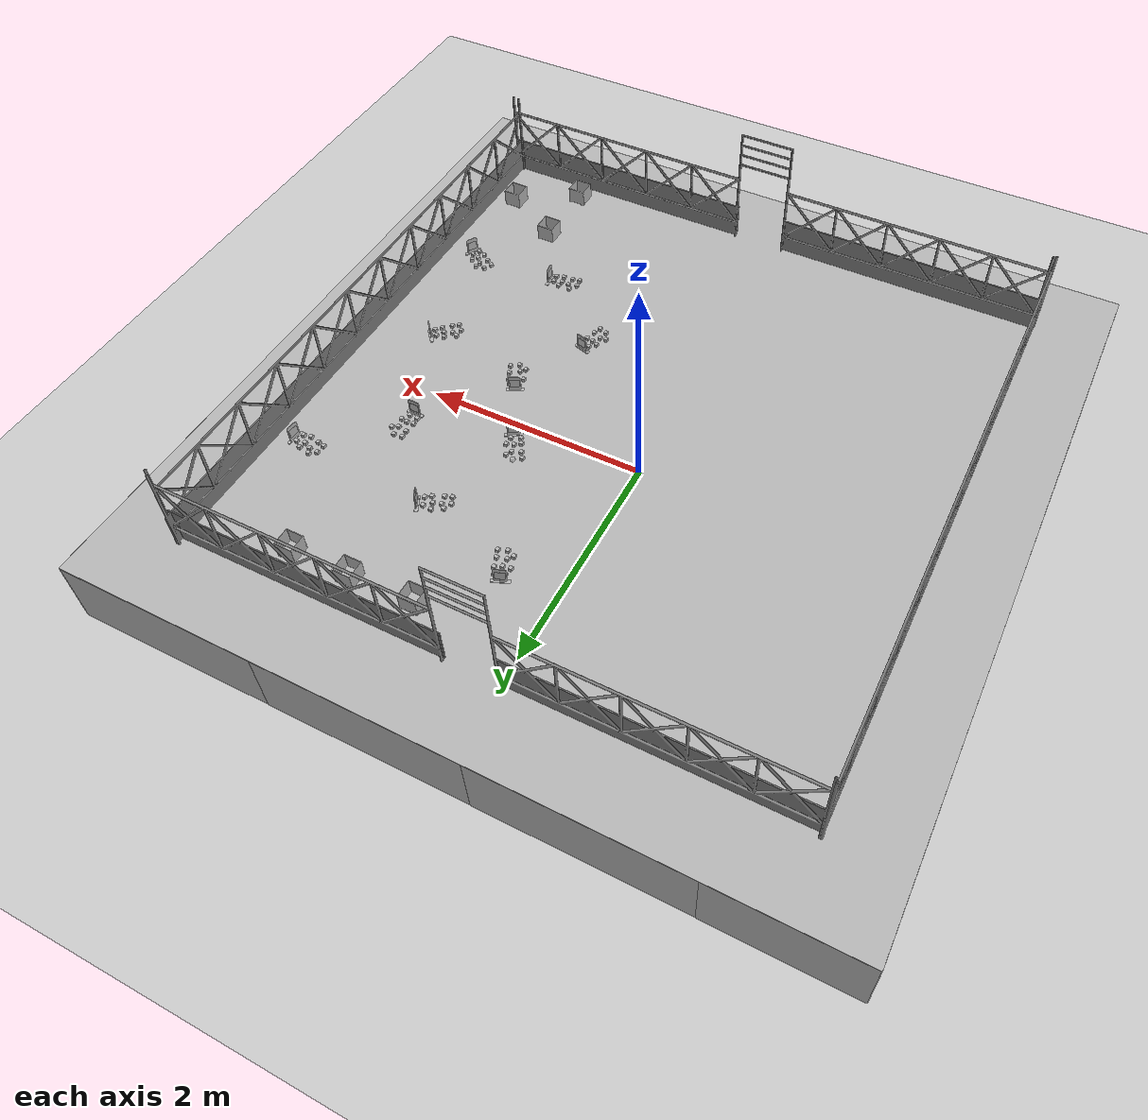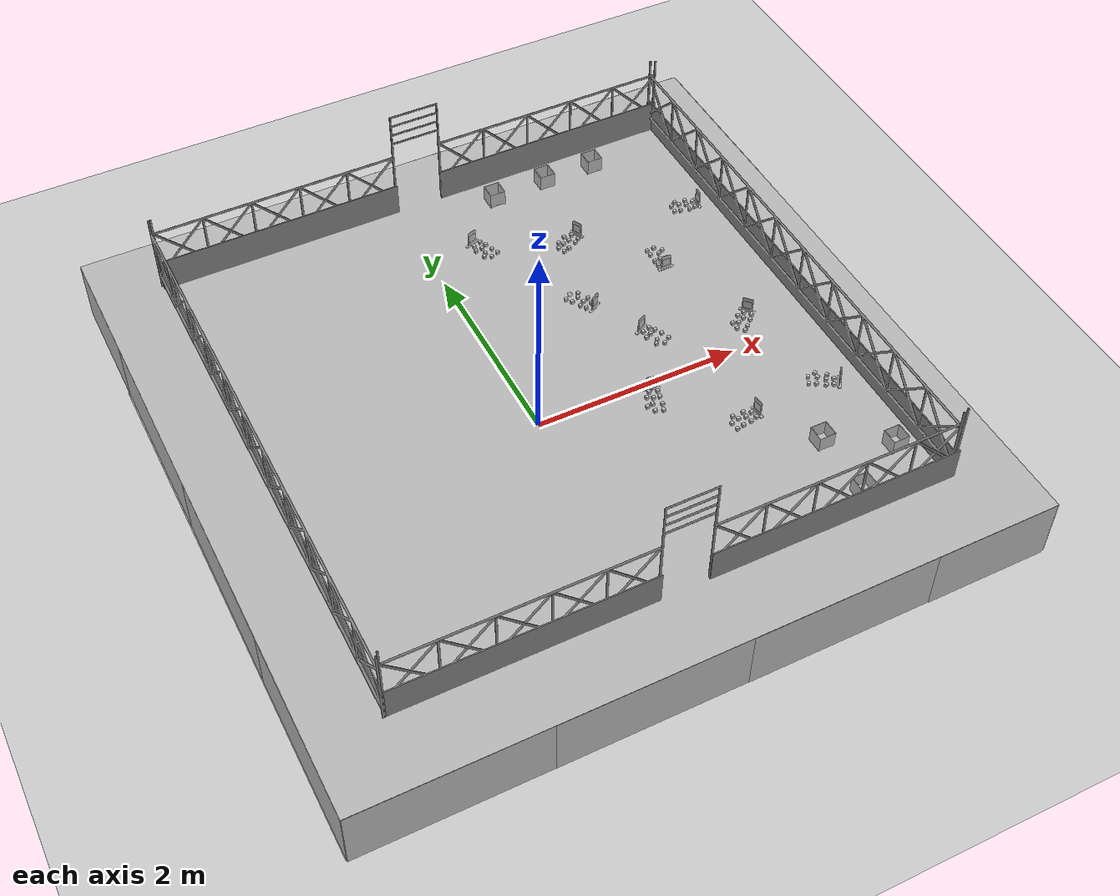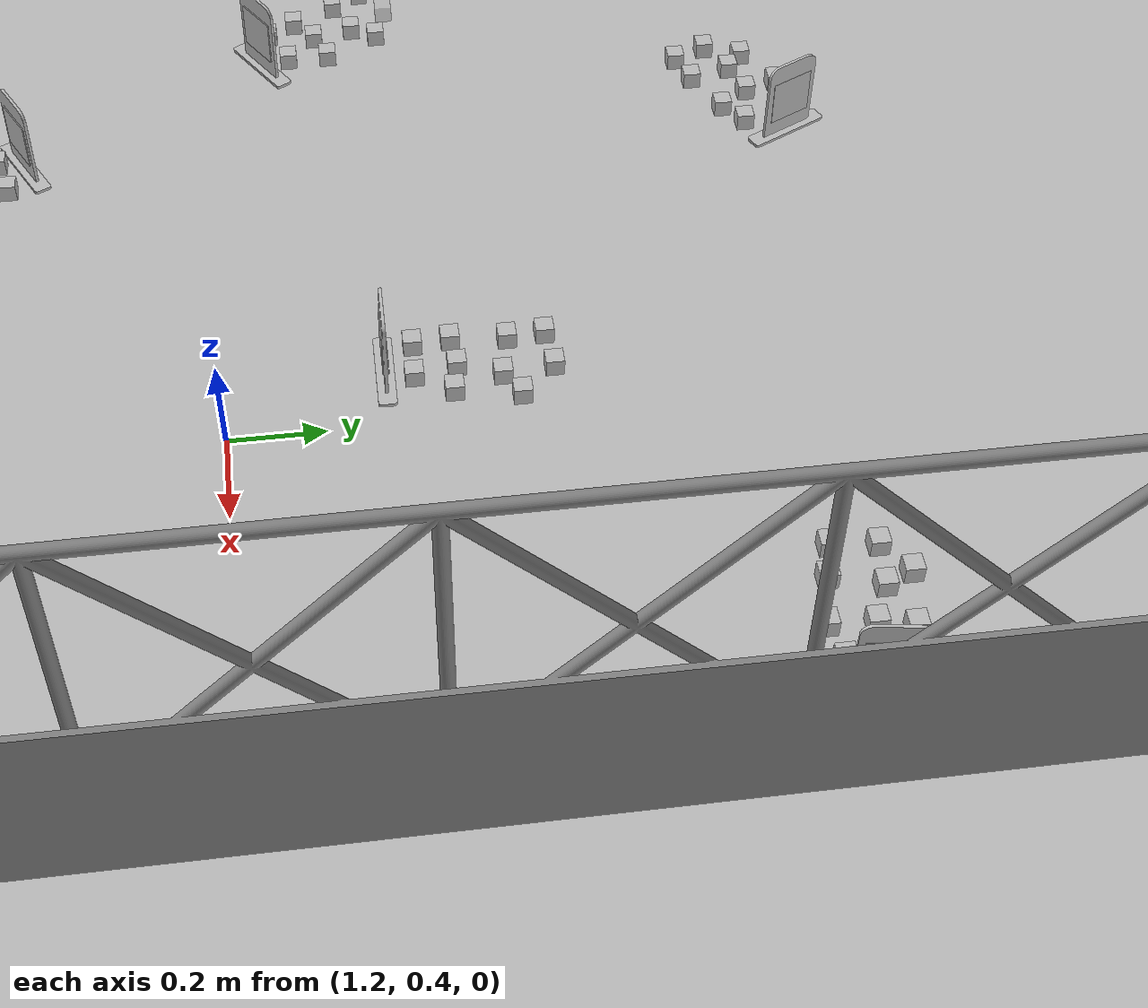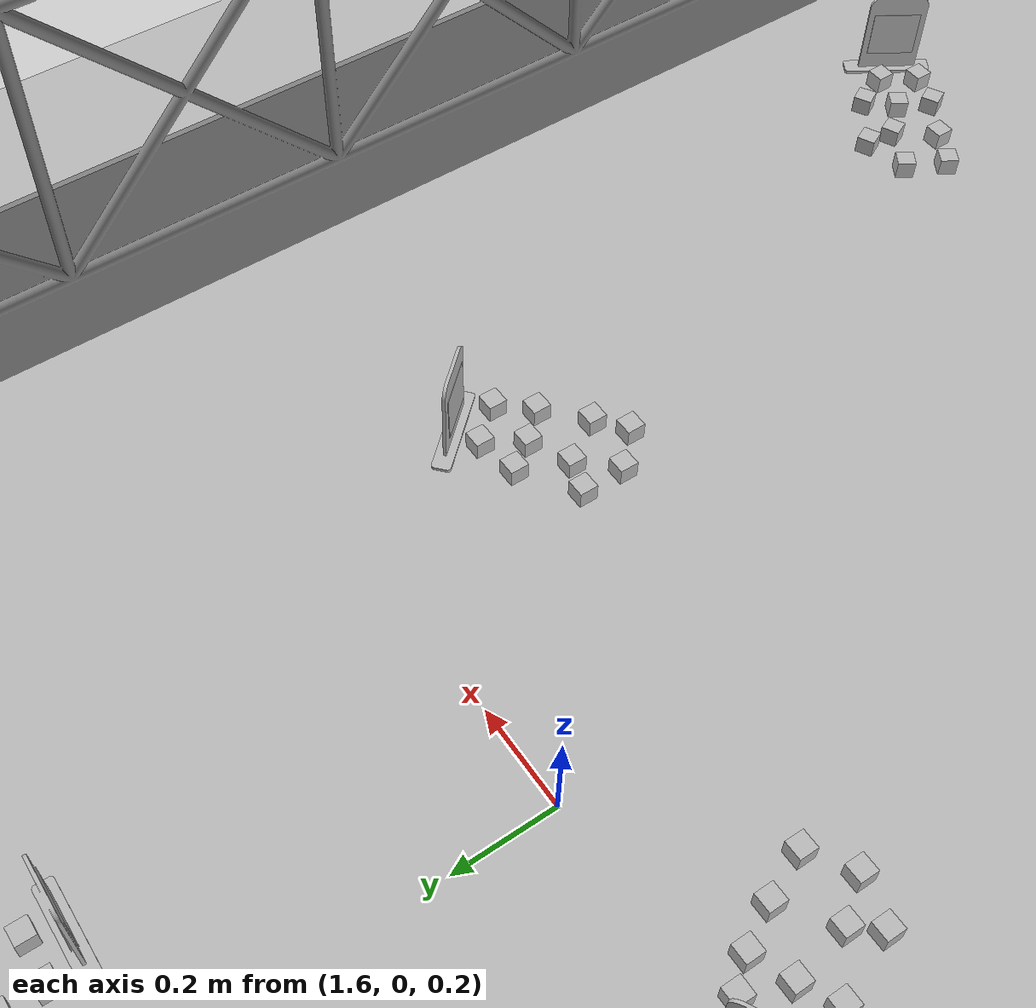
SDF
<sdf version="1.7">
 <world name="default">
  <light name="sun" type="directional">
   <pose>0 0 10 0 -0 0</pose>
   <diffuse>0.8 0.8 0.8 1</diffuse>
   <specular>0.2 0.2 0.2 1</specular>
   <attenuation>
    <range>1000</range>
    <constant>0.9</constant>
    <linear>0.01</linear>
    <quadratic>0.001</quadratic>
   </attenuation>
   <direction>-0.5 0.1 -0.9</direction>
   <spot><inner_angle>0</inner_angle><outer_angle>0</outer_angle><falloff>0</falloff></spot>
  </light>
  <model name="ground_plane">
   <static>1</static>
   <link name="link">
    <collision name="collision">
     <geometry><plane><normal>0 0 1</normal><size>100 100</size></plane></geometry>
     <surface><friction><ode><mu>100</mu><mu2>50</mu2></ode></friction></surface>
    </collision>
    <visual name="visual">
     <cast_shadows>0</cast_shadows>
     <geometry><plane><normal>0 0 1</normal><size>100 100</size></plane></geometry>
     <material>
      <script><uri>file://media/materials/scripts/gazebo.material</uri><name>Gazebo/Grey</name></script>
     </material>
    </visual>
   </link>
  </model>
  <gravity>0 0 -9.8</gravity>
  <magnetic_field>6e-06 2.3e-05 -4.2e-05</magnetic_field>
  <atmosphere type="adiabatic"/>
  <physics type="ode">
   <max_step_size>0.001</max_step_size>
   <real_time_factor>1</real_time_factor>
   <real_time_update_rate>1000</real_time_update_rate>
  </physics>
  <scene><ambient>0.4 0.4 0.4 1</ambient><background>0.7 0.7 0.7 1</background><shadows>1</shadows></scene>
  <audio><device>default</device></audio>
  <spherical_coordinates>
   <surface_model>EARTH_WGS84</surface_model>
   <latitude_deg>0</latitude_deg>
   <longitude_deg>0</longitude_deg>
   <elevation>0</elevation>
   <heading_deg>0</heading_deg>
  </spherical_coordinates>
  <model name="arene_base">
   <static>1</static>
   <link name="base_link">
    <visual name="base_visual">
     <geometry><box><size>6.25 6.25 0.6</size></box></geometry>
     <material>
      <script>
       <uri>model://arene_base/materials/scripts/</uri>
       <uri>model://arene_base/materials/textures/</uri>
       <name>arene_base/FaceMaterial</name>
      </script>
     </material>
    </visual>
    <collision name="base_collision"><geometry><box><size>6.25 6.25 0.6</size></box></geometry></collision>
   </link>
   <pose>0 0 0.31 0 -0 1.57</pose>
  </model>
  <model name="arene_frame_with_door">
   <static>1</static>
   <link name="frame_link">
    <pose>0 0 0 1.57 -0 0</pose>
    <visual name="frame_visual">
     <geometry>
      <mesh>
       <uri>model://arene_frame_with_door/meshes/arene_frame_with_door.STL</uri>
       <scale>0.001 0.001 0.001</scale>
      </mesh>
     </geometry>
     <material>
      <ambient>0.5 0.5 0.5 1</ambient>
      <diffuse>0.5 0.5 0.5 1</diffuse>
      <specular>0.5 0.5 0.5 1</specular>
     </material>
    </visual>
    <collision name="frame_collision">
     <pose>2.55 0.3 0 1.57 -0 0</pose>
     <geometry><box><size>5 0.1 0.6</size></box></geometry>
    </collision>
    <inertial>
     <mass>25</mass>
     <inertia><ixx>0</ixx><ixy>0</ixy><ixz>0</ixz><iyy>0</iyy><iyz>0</iyz><izz>0</izz></inertia>
    </inertial>
   </link>
   <pose>-2.51691 -2.45839 0.610466 0 -0 0</pose>
  </model>
  <model name="arene_frame_with_door_clone">
   <static>1</static>
   <link name="frame_link">
    <pose>0 0 0 1.57 -0 0</pose>
    <visual name="frame_visual">
     <geometry>
      <mesh>
       <uri>model://arene_frame_with_door/meshes/arene_frame_with_door.STL</uri>
       <scale>0.001 0.001 0.001</scale>
      </mesh>
     </geometry>
     <material>
      <ambient>0.5 0.5 0.5 1</ambient>
      <diffuse>0.5 0.5 0.5 1</diffuse>
      <specular>0.5 0.5 0.5 1</specular>
     </material>
    </visual>
    <collision name="frame_collision">
     <pose>2.55 0.3 0 1.57 -0 0</pose>
     <geometry><box><size>5 0.1 0.6</size></box></geometry>
    </collision>
    <inertial>
     <mass>25</mass>
     <inertia><ixx>0</ixx><ixy>0</ixy><ixz>0</ixz><iyy>0</iyy><iyz>0</iyz><izz>0</izz></inertia>
    </inertial>
   </link>
   <pose>-2.52448 2.54082 0.610466 0 -0 0</pose>
  </model>
  <model name="arene_frame">
   <static>1</static>
   <link name="frame_link">
    <pose>0 0 0 1.57 -0 0</pose>
    <visual name="frame_visual">
     <geometry>
      <mesh><uri>model://arene_frame/meshes/arene_frame.STL</uri><scale>0.001 0.001 0.001</scale></mesh>
     </geometry>
     <material>
      <ambient>0.5 0.5 0.5 1</ambient>
      <diffuse>0.5 0.5 0.5 1</diffuse>
      <specular>0.5 0.5 0.5 1</specular>
     </material>
    </visual>
    <collision name="frame_collision">
     <pose>2.55 0.3 0 1.57 -0 0</pose>
     <geometry><box><size>5 0.1 0.6</size></box></geometry>
    </collision>
    <inertial>
     <mass>25</mass>
     <inertia><ixx>0</ixx><ixy>0</ixy><ixz>0</ixz><iyy>0</iyy><iyz>0</iyz><izz>0</izz></inertia>
    </inertial>
   </link>
   <pose>2.47831 -2.49008 0.601132 0 -0 1.57059</pose>
  </model>
  <model name="arene_frame_clone">
   <static>1</static>
   <link name="frame_link">
    <pose>0 0 0 1.57 -0 0</pose>
    <visual name="frame_visual">
     <geometry>
      <mesh><uri>model://arene_frame/meshes/arene_frame.STL</uri><scale>0.001 0.001 0.001</scale></mesh>
     </geometry>
     <material>
      <ambient>0.5 0.5 0.5 1</ambient>
      <diffuse>0.5 0.5 0.5 1</diffuse>
      <specular>0.5 0.5 0.5 1</specular>
     </material>
    </visual>
    <collision name="frame_collision">
     <pose>2.55 0.3 0 1.57 -0 0</pose>
     <geometry><box><size>5 0.1 0.6</size></box></geometry>
    </collision>
    <inertial>
     <mass>25</mass>
     <inertia><ixx>0</ixx><ixy>0</ixy><ixz>0</ixz><iyy>0</iyy><iyz>0</iyz><izz>0</izz></inertia>
    </inertial>
   </link>
   <pose>-2.53905 -2.50495 0.601132 0 -0 1.57059</pose>
  </model>
  <model name="pancarte_qr_code_haie-vive">
   <pose>2.28267 -1.19625 0.649378 0 0 -2.13591</pose>
   <model name="pancarte">
    <static>1</static>
    <link name="link">
     <collision name="collision">
      <pose>0 0.075 0 0 -0 0</pose>
      <geometry><box><size>0.15 0.15 0.03</size></box></geometry>
     </collision>
     <visual name="visual">
      <geometry>
       <mesh><scale>0.001 0.001 0.001</scale><uri>model://pancarte/meshes/PANCARTE_QR.stl</uri></mesh>
      </geometry>
     </visual>
    </link>
    <pose>8.8e-05 0.001115 -0.037644 1.55978 -0 0</pose>
   </model>
   <model name="qr_code_zone1Haie-Vive">
    <static>1</static>
    <link name="qr_code_zone1Haie-Vive_link">
     <pose>0 0 0.001 0 -0 1.5708</pose>
     <visual name="visual_qr_code_zone1Haie-Vive">
      <cast_shadows>0</cast_shadows>
      <geometry><box><size>0.08 0.08 0.001</size></box></geometry>
      <material>
       <script>
        <uri>model://qr_code_zone1Haie-Vive/materials/scripts</uri>
        <uri>model://qr_code_zone1Haie-Vive/materials/textures</uri>
        <name>qr_code_zone1Haie-Vive/qr_code_zone1Haie-Vive</name>
       </script>
      </material>
     </visual>
    </link>
    <pose>-8.8e-05 -0.001115 0.037644 1.55615 -0 0</pose>
   </model>
   <model name="qr_code_zone1Haie-Vive_0">
    <static>1</static>
    <link name="qr_code_zone1Haie-Vive_link">
     <pose>0 0 0.001 0 -0 1.5708</pose>
     <visual name="visual_qr_code_zone1Haie-Vive">
      <cast_shadows>0</cast_shadows>
      <geometry><box><size>0.08 0.08 0.001</size></box></geometry>
      <material>
       <script>
        <uri>model://qr_code_zone1Haie-Vive/materials/scripts</uri>
        <uri>model://qr_code_zone1Haie-Vive/materials/textures</uri>
        <name>qr_code_zone1Haie-Vive/qr_code_zone1Haie-Vive</name>
       </script>
      </material>
     </visual>
    </link>
    <pose>-8.8e-05 0.0072 0.037644 -1.58544 0.001593 3.14159</pose>
   </model>
   <static>0</static>
  </model>
  <model name="menagers_commerciale_barquette_salade">
   <static>0</static>
   <link name="link">
    <inertial>
     <mass>0.00893</mass>
     <inertia>
      <ixx>4.47e-06</ixx>
      <iyy>4.47e-06</iyy>
      <izz>4.47e-06</izz>
      <ixy>0</ixy>
      <ixz>0</ixz>
      <iyz>0</iyz>
     </inertia>
    </inertial>
    <visual name="cube_visual">
     <geometry><box><size>0.03 0.03 0.03</size></box></geometry>
     <material>
      <script>
       <uri>model://menagers_commerciale_barquette_salade/materials/scripts/</uri>
       <uri>model://menagers_commerciale_barquette_salade/materials/textures/</uri>
       <name>menagers_commerciale_barquette_salade/FaceMaterial</name>
      </script>
     </material>
    </visual>
    <collision name="collision"><geometry><box><size>0.03 0.03 0.03</size></box></geometry></collision>
   </link>
   <pose>2.25529 -1.15391 0.625 -0 -0 -0.009215</pose>
  </model>
  <model name="menagers_commerciale_boite_pizza">
   <static>0</static>
   <link name="link">
    <inertial>
     <mass>0.00893</mass>
     <inertia>
      <ixx>4.47e-06</ixx>
      <iyy>4.47e-06</iyy>
      <izz>4.47e-06</izz>
      <ixy>0</ixy>
      <ixz>0</ixz>
      <iyz>0</iyz>
     </inertia>
    </inertial>
    <visual name="cube_visual">
     <geometry><box><size>0.03 0.03 0.03</size></box></geometry>
     <material>
      <script>
       <uri>model://menagers_commerciale_boite_pizza/materials/scripts/</uri>
       <uri>model://menagers_commerciale_boite_pizza/materials/textures/</uri>
       <name>menagers_commerciale_boite_pizza/FaceMaterial</name>
      </script>
     </material>
    </visual>
    <collision name="collision"><geometry><box><size>0.03 0.03 0.03</size></box></geometry></collision>
   </link>
   <pose>2.22572 -1.09026 0.625 -1e-06 7e-06 0.495794</pose>
  </model>
  <model name="menagers_residentielle_barquette_viande">
   <static>0</static>
   <link name="link">
    <inertial>
     <mass>0.00893</mass>
     <inertia>
      <ixx>4.47e-06</ixx>
      <iyy>4.47e-06</iyy>
      <izz>4.47e-06</izz>
      <ixy>0</ixy>
      <ixz>0</ixz>
      <iyz>0</iyz>
     </inertia>
    </inertial>
    <visual name="cube_visual">
     <geometry><box><size>0.03 0.03 0.03</size></box></geometry>
     <material>
      <script>
       <uri>model://menagers_residentielle_barquette_viande/materials/scripts/</uri>
       <uri>model://menagers_residentielle_barquette_viande/materials/textures/</uri>
       <name>menagers_residentielle_barquette_viande/FaceMaterial</name>
      </script>
     </material>
    </visual>
    <collision name="collision"><geometry><box><size>0.03 0.03 0.03</size></box></geometry></collision>
   </link>
   <pose>2.22021 -1.21042 0.625 0 -0 -0.006621</pose>
  </model>
  <model name="menagers_residentielle_boite_cereales">
   <static>0</static>
   <link name="link">
    <inertial>
     <mass>0.00893</mass>
     <inertia>
      <ixx>4.47e-06</ixx>
      <iyy>4.47e-06</iyy>
      <izz>4.47e-06</izz>
      <ixy>0</ixy>
      <ixz>0</ixz>
      <iyz>0</iyz>
     </inertia>
    </inertial>
    <visual name="cube_visual">
     <geometry><box><size>0.03 0.03 0.03</size></box></geometry>
     <material>
      <script>
       <uri>model://menagers_residentielle_boite_cereales/materials/scripts/</uri>
       <uri>model://menagers_residentielle_boite_cereales/materials/textures/</uri>
       <name>menagers_residentielle_boite_cereales/FaceMaterial</name>
      </script>
     </material>
    </visual>
    <collision name="collision"><geometry><box><size>0.03 0.03 0.03</size></box></geometry></collision>
   </link>
   <pose>2.18776 -1.13221 0.624992 -1.6e-05 0.000109 -0.579343</pose>
  </model>
  <model name="menagers_industrielle_bidon_eau_5L">
   <static>0</static>
   <link name="link">
    <inertial>
     <mass>0.00893</mass>
     <inertia>
      <ixx>4.47e-06</ixx>
      <iyy>4.47e-06</iyy>
      <izz>4.47e-06</izz>
      <ixy>0</ixy>
      <ixz>0</ixz>
      <iyz>0</iyz>
     </inertia>
    </inertial>
    <visual name="cube_visual">
     <geometry><box><size>0.03 0.03 0.03</size></box></geometry>
     <material>
      <script>
       <uri>model://menagers_industrielle_bidon_eau_5L/materials/scripts/</uri>
       <uri>model://menagers_industrielle_bidon_eau_5L/materials/textures/</uri>
       <name>menagers_industrielle_bidon_eau_5L/FaceMaterial</name>
      </script>
     </material>
    </visual>
    <collision name="collision"><geometry><box><size>0.03 0.03 0.03</size></box></geometry></collision>
   </link>
   <pose>2.15921 -1.18684 0.624992 0.000122 -1e-06 0.453067</pose>
  </model>
  <model name="recyclables_commerciale_bouteille_eau_propre">
   <static>0</static>
   <link name="link">
    <inertial>
     <mass>0.00893</mass>
     <inertia>
      <ixx>4.47e-06</ixx>
      <iyy>4.47e-06</iyy>
      <izz>4.47e-06</izz>
      <ixy>0</ixy>
      <ixz>0</ixz>
      <iyz>0</iyz>
     </inertia>
    </inertial>
    <visual name="cube_visual">
     <geometry><box><size>0.03 0.03 0.03</size></box></geometry>
     <material>
      <script>
       <uri>model://recyclables_commerciale_bouteille_eau_propre/materials/scripts/</uri>
       <uri>model://recyclables_commerciale_bouteille_eau_propre/materials/textures/</uri>
       <name>recyclables_commerciale_bouteille_eau_propre/FaceMaterial</name>
      </script>
     </material>
    </visual>
    <collision name="collision"><geometry><box><size>0.03 0.03 0.03</size></box></geometry></collision>
   </link>
   <pose>2.09062 -1.13706 0.624996 -9.7e-05 -1e-06 -0.000868</pose>
  </model>
  <model name="recyclables_industrielle_aluminium_industriel">
   <static>0</static>
   <link name="link">
    <inertial>
     <mass>0.00893</mass>
     <inertia>
      <ixx>4.47e-06</ixx>
      <iyy>4.47e-06</iyy>
      <izz>4.47e-06</izz>
      <ixy>0</ixy>
      <ixz>0</ixz>
      <iyz>0</iyz>
     </inertia>
    </inertial>
    <visual name="cube_visual">
     <geometry><box><size>0.03 0.03 0.03</size></box></geometry>
     <material>
      <script>
       <uri>model://recyclables_industrielle_aluminium_industriel/materials/scripts/</uri>
       <uri>model://recyclables_industrielle_aluminium_industriel/materials/textures/</uri>
       <name>recyclables_industrielle_aluminium_industriel/FaceMaterial</name>
      </script>
     </material>
    </visual>
    <collision name="collision"><geometry><box><size>0.03 0.03 0.03</size></box></geometry></collision>
   </link>
   <pose>2.03343 -1.10231 0.624999 -1.7e-05 -0 -0.540505</pose>
  </model>
  <model name="recyclables_residentielle_bocal_verre_propre">
   <static>0</static>
   <link name="link">
    <inertial>
     <mass>0.00893</mass>
     <inertia>
      <ixx>4.47e-06</ixx>
      <iyy>4.47e-06</iyy>
      <izz>4.47e-06</izz>
      <ixy>0</ixy>
      <ixz>0</ixz>
      <iyz>0</iyz>
     </inertia>
    </inertial>
    <visual name="cube_visual">
     <geometry><box><size>0.03 0.03 0.03</size></box></geometry>
     <material>
      <script>
       <uri>model://recyclables_residentielle_bocal_verre_propre/materials/scripts/</uri>
       <uri>model://recyclables_residentielle_bocal_verre_propre/materials/textures/</uri>
       <name>recyclables_residentielle_bocal_verre_propre/FaceMaterial</name>
      </script>
     </material>
    </visual>
    <collision name="collision"><geometry><box><size>0.03 0.03 0.03</size></box></geometry></collision>
   </link>
   <pose>2.14456 -1.02571 0.624992 7.9e-05 3e-06 0.442661</pose>
  </model>
  <model name="dangereux_commerciale_batterie_ordinateur">
   <static>0</static>
   <link name="link">
    <inertial>
     <mass>0.00893</mass>
     <inertia>
      <ixx>4.47e-06</ixx>
      <iyy>4.47e-06</iyy>
      <izz>4.47e-06</izz>
      <ixy>0</ixy>
      <ixz>0</ixz>
      <iyz>0</iyz>
     </inertia>
    </inertial>
    <visual name="cube_visual">
     <geometry><box><size>0.03 0.03 0.03</size></box></geometry>
     <material>
      <script>
       <uri>model://dangereux_commerciale_batterie_ordinateur/materials/scripts/</uri>
       <uri>model://dangereux_commerciale_batterie_ordinateur/materials/textures/</uri>
       <name>dangereux_commerciale_batterie_ordinateur/FaceMaterial</name>
      </script>
     </material>
    </visual>
    <collision name="collision"><geometry><box><size>0.03 0.03 0.03</size></box></geometry></collision>
   </link>
   <pose>2.13963 -1.07675 0.624997 0.000127 4e-06 0.410696</pose>
  </model>
  <model name="dangereux_industrielle_amiante_plaque">
   <static>0</static>
   <link name="link">
    <inertial>
     <mass>0.00893</mass>
     <inertia>
      <ixx>4.47e-06</ixx>
      <iyy>4.47e-06</iyy>
      <izz>4.47e-06</izz>
      <ixy>0</ixy>
      <ixz>0</ixz>
      <iyz>0</iyz>
     </inertia>
    </inertial>
    <visual name="cube_visual">
     <geometry><box><size>0.03 0.03 0.03</size></box></geometry>
     <material>
      <script>
       <uri>model://dangereux_industrielle_amiante_plaque/materials/scripts/</uri>
       <uri>model://dangereux_industrielle_amiante_plaque/materials/textures/</uri>
       <name>dangereux_industrielle_amiante_plaque/FaceMaterial</name>
      </script>
     </material>
    </visual>
    <collision name="collision"><geometry><box><size>0.03 0.03 0.03</size></box></geometry></collision>
   </link>
   <pose>2.06779 -1.03809 0.624998 3.2e-05 8.5e-05 -0.589509</pose>
  </model>
  <model name="pancarte_qr_code_zone1Tampouy">
   <pose>2.02917 -0.098874 0.649378 0 -0 2.30094</pose>
   <model name="pancarte">
    <static>1</static>
    <link name="pancarte_qr_code_zone1Tampouy_link">
     <collision name="collision">
      <pose>0 0.075 0 0 -0 0</pose>
      <geometry><box><size>0.15 0.15 0.03</size></box></geometry>
     </collision>
     <visual name="visual">
      <geometry>
       <mesh><scale>0.001 0.001 0.001</scale><uri>model://pancarte/meshes/PANCARTE_QR.stl</uri></mesh>
      </geometry>
     </visual>
    </link>
    <pose>8.8e-05 0.001115 -0.037644 1.55978 -0 0</pose>
   </model>
   <model name="qr_code_zone1Tampouy">
    <static>1</static>
    <link name="qr_code_zone1Tampouy_link">
     <pose>0 0 0.001 0 -0 1.5708</pose>
     <visual name="visual_qr_code_zone1Tampouy">
      <cast_shadows>0</cast_shadows>
      <geometry><box><size>0.08 0.08 0.001</size></box></geometry>
      <material>
       <script>
        <uri>model://qr_code_zone1Tampouy/materials/scripts</uri>
        <uri>model://qr_code_zone1Tampouy/materials/textures</uri>
        <name>qr_code_zone1Tampouy/qr_code_zone1Tampouy</name>
       </script>
      </material>
     </visual>
    </link>
    <pose>-8.8e-05 -0.001115 0.037644 1.55615 -0 0</pose>
   </model>
   <model name="qr_code_zone1Tampouy_0">
    <static>1</static>
    <link name="qr_code_zone1Tampouy_link">
     <pose>0 0 0.001 0 -0 1.5708</pose>
     <visual name="visual_qr_code_zone1Tampouy">
      <cast_shadows>0</cast_shadows>
      <geometry><box><size>0.08 0.08 0.001</size></box></geometry>
      <material>
       <script>
        <uri>model://qr_code_zone1Tampouy/materials/scripts</uri>
        <uri>model://qr_code_zone1Tampouy/materials/textures</uri>
        <name>qr_code_zone1Tampouy/qr_code_zone1Tampouy</name>
       </script>
      </material>
     </visual>
    </link>
    <pose>-8.8e-05 0.0072 0.037644 -1.58544 0.001593 3.14159</pose>
   </model>
   <static>0</static>
  </model>
  <model name="menagers_commerciale_bouteille_jus">
   <static>0</static>
   <link name="link">
    <inertial>
     <mass>0.00893</mass>
     <inertia>
      <ixx>4.47e-06</ixx>
      <iyy>4.47e-06</iyy>
      <izz>4.47e-06</izz>
      <ixy>0</ixy>
      <ixz>0</ixz>
      <iyz>0</iyz>
     </inertia>
    </inertial>
    <visual name="cube_visual">
     <geometry><box><size>0.03 0.03 0.03</size></box></geometry>
     <material>
      <script>
       <uri>model://menagers_commerciale_bouteille_jus/materials/scripts/</uri>
       <uri>model://menagers_commerciale_bouteille_jus/materials/textures/</uri>
       <name>menagers_commerciale_bouteille_jus/FaceMaterial</name>
      </script>
     </material>
    </visual>
    <collision name="collision"><geometry><box><size>0.03 0.03 0.03</size></box></geometry></collision>
   </link>
   <pose>1.87732 -0.313326 0.625 -0 -0 -0.002421</pose>
  </model>
  <model name="menagers_industrielle_bidon_huile_moteur">
   <static>0</static>
   <link name="link">
    <inertial>
     <mass>0.00893</mass>
     <inertia>
      <ixx>4.47e-06</ixx>
      <iyy>4.47e-06</iyy>
      <izz>4.47e-06</izz>
      <ixy>0</ixy>
      <ixz>0</ixz>
      <iyz>0</iyz>
     </inertia>
    </inertial>
    <visual name="cube_visual">
     <geometry><box><size>0.03 0.03 0.03</size></box></geometry>
     <material>
      <script>
       <uri>model://menagers_industrielle_bidon_huile_moteur/materials/scripts/</uri>
       <uri>model://menagers_industrielle_bidon_huile_moteur/materials/textures/</uri>
       <name>menagers_industrielle_bidon_huile_moteur/FaceMaterial</name>
      </script>
     </material>
    </visual>
    <collision name="collision"><geometry><box><size>0.03 0.03 0.03</size></box></geometry></collision>
   </link>
   <pose>1.92313 -0.277239 0.625 0 -0 -0.00668</pose>
  </model>
  <model name="menagers_industrielle_big_bag_vide">
   <static>0</static>
   <link name="link">
    <inertial>
     <mass>0.00893</mass>
     <inertia>
      <ixx>4.47e-06</ixx>
      <iyy>4.47e-06</iyy>
      <izz>4.47e-06</izz>
      <ixy>0</ixy>
      <ixz>0</ixz>
      <iyz>0</iyz>
     </inertia>
    </inertial>
    <visual name="cube_visual">
     <geometry><box><size>0.03 0.03 0.03</size></box></geometry>
     <material>
      <script>
       <uri>model://menagers_industrielle_big_bag_vide/materials/scripts/</uri>
       <uri>model://menagers_industrielle_big_bag_vide/materials/textures/</uri>
       <name>menagers_industrielle_big_bag_vide/FaceMaterial</name>
      </script>
     </material>
    </visual>
    <collision name="collision"><geometry><box><size>0.03 0.03 0.03</size></box></geometry></collision>
   </link>
   <pose>1.87718 -0.206616 0.625 0 -0 -0.00668</pose>
  </model>
  <model name="menagers_commerciale_bouteille_smoothie">
   <static>0</static>
   <link name="link">
    <inertial>
     <mass>0.00893</mass>
     <inertia>
      <ixx>4.47e-06</ixx>
      <iyy>4.47e-06</iyy>
      <izz>4.47e-06</izz>
      <ixy>0</ixy>
      <ixz>0</ixz>
      <iyz>0</iyz>
     </inertia>
    </inertial>
    <visual name="cube_visual">
     <geometry><box><size>0.03 0.03 0.03</size></box></geometry>
     <material>
      <script>
       <uri>model://menagers_commerciale_bouteille_smoothie/materials/scripts/</uri>
       <uri>model://menagers_commerciale_bouteille_smoothie/materials/textures/</uri>
       <name>menagers_commerciale_bouteille_smoothie/FaceMaterial</name>
      </script>
     </material>
    </visual>
    <collision name="collision"><geometry><box><size>0.03 0.03 0.03</size></box></geometry></collision>
   </link>
   <pose>1.98228 -0.11628 0.624997 -3.5e-05 -2.2e-05 -0.000421</pose>
  </model>
  <model name="menagers_residentielle_boite_conserve_tomate">
   <static>0</static>
   <link name="link">
    <inertial>
     <mass>0.00893</mass>
     <inertia>
      <ixx>4.47e-06</ixx>
      <iyy>4.47e-06</iyy>
      <izz>4.47e-06</izz>
      <ixy>0</ixy>
      <ixz>0</ixz>
      <iyz>0</iyz>
     </inertia>
    </inertial>
    <visual name="cube_visual">
     <geometry><box><size>0.03 0.03 0.03</size></box></geometry>
     <material>
      <script>
       <uri>model://menagers_residentielle_boite_conserve_tomate/materials/scripts/</uri>
       <uri>model://menagers_residentielle_boite_conserve_tomate/materials/textures/</uri>
       <name>menagers_residentielle_boite_conserve_tomate/FaceMaterial</name>
      </script>
     </material>
    </visual>
    <collision name="collision"><geometry><box><size>0.03 0.03 0.03</size></box></geometry></collision>
   </link>
   <pose>1.94428 -0.175542 0.624991 1.8e-05 0 -0.004042</pose>
  </model>
  <model name="menagers_residentielle_bouteille_huile">
   <static>0</static>
   <link name="link">
    <inertial>
     <mass>0.00893</mass>
     <inertia>
      <ixx>4.47e-06</ixx>
      <iyy>4.47e-06</iyy>
      <izz>4.47e-06</izz>
      <ixy>0</ixy>
      <ixz>0</ixz>
      <iyz>0</iyz>
     </inertia>
    </inertial>
    <visual name="cube_visual">
     <geometry><box><size>0.03 0.03 0.03</size></box></geometry>
     <material>
      <script>
       <uri>model://menagers_residentielle_bouteille_huile/materials/scripts/</uri>
       <uri>model://menagers_residentielle_bouteille_huile/materials/textures/</uri>
       <name>menagers_residentielle_bouteille_huile/FaceMaterial</name>
      </script>
     </material>
    </visual>
    <collision name="collision"><geometry><box><size>0.03 0.03 0.03</size></box></geometry></collision>
   </link>
   <pose>1.91332 -0.129687 0.624991 1.8e-05 0 -0.004042</pose>
  </model>
  <model name="recyclables_commerciale_bouteille_verre_biere">
   <static>0</static>
   <link name="link">
    <inertial>
     <mass>0.00893</mass>
     <inertia>
      <ixx>4.47e-06</ixx>
      <iyy>4.47e-06</iyy>
      <izz>4.47e-06</izz>
      <ixy>0</ixy>
      <ixz>0</ixz>
      <iyz>0</iyz>
     </inertia>
    </inertial>
    <visual name="cube_visual">
     <geometry><box><size>0.03 0.03 0.03</size></box></geometry>
     <material>
      <script>
       <uri>model://recyclables_commerciale_bouteille_verre_biere/materials/scripts/</uri>
       <uri>model://recyclables_commerciale_bouteille_verre_biere/materials/textures/</uri>
       <name>recyclables_commerciale_bouteille_verre_biere/FaceMaterial</name>
      </script>
     </material>
    </visual>
    <collision name="collision"><geometry><box><size>0.03 0.03 0.03</size></box></geometry></collision>
   </link>
   <pose>1.8262 -0.189412 0.624991 -0 7.7e-05 -0.002275</pose>
  </model>
  <model name="recyclables_industrielle_bronze_industriel">
   <static>0</static>
   <link name="link">
    <inertial>
     <mass>0.00893</mass>
     <inertia>
      <ixx>4.47e-06</ixx>
      <iyy>4.47e-06</iyy>
      <izz>4.47e-06</izz>
      <ixy>0</ixy>
      <ixz>0</ixz>
      <iyz>0</iyz>
     </inertia>
    </inertial>
    <visual name="cube_visual">
     <geometry><box><size>0.03 0.03 0.03</size></box></geometry>
     <material>
      <script>
       <uri>model://recyclables_industrielle_bronze_industriel/materials/scripts/</uri>
       <uri>model://recyclables_industrielle_bronze_industriel/materials/textures/</uri>
       <name>recyclables_industrielle_bronze_industriel/FaceMaterial</name>
      </script>
     </material>
    </visual>
    <collision name="collision"><geometry><box><size>0.03 0.03 0.03</size></box></geometry></collision>
   </link>
   <pose>1.82664 -0.261894 0.625 -0 -0 -0.008562</pose>
  </model>
  <model name="dangereux_commerciale_batterie_ups">
   <static>0</static>
   <link name="link">
    <inertial>
     <mass>0.00893</mass>
     <inertia>
      <ixx>4.47e-06</ixx>
      <iyy>4.47e-06</iyy>
      <izz>4.47e-06</izz>
      <ixy>0</ixy>
      <ixz>0</ixz>
      <iyz>0</iyz>
     </inertia>
    </inertial>
    <visual name="cube_visual">
     <geometry><box><size>0.03 0.03 0.03</size></box></geometry>
     <material>
      <script>
       <uri>model://dangereux_commerciale_batterie_ups/materials/scripts/</uri>
       <uri>model://dangereux_commerciale_batterie_ups/materials/textures/</uri>
       <name>dangereux_commerciale_batterie_ups/FaceMaterial</name>
      </script>
     </material>
    </visual>
    <collision name="collision"><geometry><box><size>0.03 0.03 0.03</size></box></geometry></collision>
   </link>
   <pose>2.02923 -0.171082 0.624997 -5.9e-05 1e-05 -0.001047</pose>
  </model>
  <model name="dangereux_residentielle_aerosol_vide">
   <static>0</static>
   <link name="link">
    <inertial>
     <mass>0.00893</mass>
     <inertia>
      <ixx>4.47e-06</ixx>
      <iyy>4.47e-06</iyy>
      <izz>4.47e-06</izz>
      <ixy>0</ixy>
      <ixz>0</ixz>
      <iyz>0</iyz>
     </inertia>
    </inertial>
    <visual name="cube_visual">
     <geometry><box><size>0.03 0.03 0.03</size></box></geometry>
     <material>
      <script>
       <uri>model://dangereux_residentielle_aerosol_vide/materials/scripts/</uri>
       <uri>model://dangereux_residentielle_aerosol_vide/materials/textures/</uri>
       <name>dangereux_residentielle_aerosol_vide/FaceMaterial</name>
      </script>
     </material>
    </visual>
    <collision name="collision"><geometry><box><size>0.03 0.03 0.03</size></box></geometry></collision>
   </link>
   <pose>1.98517 -0.220172 0.624995 -5.8e-05 3e-06 -0.001087</pose>
  </model>
  <model name="pancarte_qr_code_erevan">
   <pose>1.46903 -1.17704 0.649378 0 -0 -1.46783</pose>
   <model name="pancarte">
    <static>1</static>
    <link name="link">
     <collision name="collision">
      <pose>0 0.075 0 0 -0 0</pose>
      <geometry><box><size>0.15 0.15 0.03</size></box></geometry>
     </collision>
     <visual name="visual">
      <geometry>
       <mesh><scale>0.001 0.001 0.001</scale><uri>model://pancarte/meshes/PANCARTE_QR.stl</uri></mesh>
      </geometry>
     </visual>
    </link>
    <pose>8.8e-05 0.001115 -0.037644 1.55978 -0 0</pose>
   </model>
   <model name="qr_code_zone1Erevan">
    <static>1</static>
    <link name="qr_code_zone1Erevan_link">
     <pose>0 0 0.001 0 -0 1.5708</pose>
     <visual name="visual_qr_code_zone1Erevan">
      <cast_shadows>0</cast_shadows>
      <geometry><box><size>0.08 0.08 0.001</size></box></geometry>
      <material>
       <script>
        <uri>model://qr_code_zone1Erevan/materials/scripts</uri>
        <uri>model://qr_code_zone1Erevan/materials/textures</uri>
        <name>qr_code_zone1Erevan/qr_code_zone1Erevan</name>
       </script>
      </material>
     </visual>
    </link>
    <pose>-8.8e-05 -0.001115 0.037644 1.55615 -0 0</pose>
   </model>
   <model name="qr_code_zone1Erevan_0">
    <static>1</static>
    <link name="qr_code_zone1Erevan_link">
     <pose>0 0 0.001 0 -0 1.5708</pose>
     <visual name="visual_qr_code_zone1Erevan">
      <cast_shadows>0</cast_shadows>
      <geometry><box><size>0.08 0.08 0.001</size></box></geometry>
      <material>
       <script>
        <uri>model://qr_code_zone1Erevan/materials/scripts</uri>
        <uri>model://qr_code_zone1Erevan/materials/textures</uri>
        <name>qr_code_zone1Erevan/qr_code_zone1Erevan</name>
       </script>
      </material>
     </visual>
    </link>
    <pose>-8.8e-05 0.0072 0.037644 -1.58544 0.001593 3.14159</pose>
   </model>
   <static>0</static>
  </model>
  <model name="pancarte_qr_code_zone2Missebo">
   <pose>2.3585 1.34573 0.649378 -0 -0 -1.71538</pose>
   <model name="pancarte">
    <static>1</static>
    <link name="link">
     <collision name="collision">
      <pose>0 0.075 0 0 -0 0</pose>
      <geometry><box><size>0.15 0.15 0.03</size></box></geometry>
     </collision>
     <visual name="visual">
      <geometry>
       <mesh><scale>0.001 0.001 0.001</scale><uri>model://pancarte/meshes/PANCARTE_QR.stl</uri></mesh>
      </geometry>
     </visual>
    </link>
    <pose>8.8e-05 0.001115 -0.037644 1.55978 -0 0</pose>
   </model>
   <model name="qr_code_zone2Missebo">
    <static>1</static>
    <link name="qr_code_zone2Missebo_link">
     <pose>0 0 0.001 0 -0 1.5708</pose>
     <visual name="visual_qr_code_zone2Missebo">
      <cast_shadows>0</cast_shadows>
      <geometry><box><size>0.08 0.08 0.001</size></box></geometry>
      <material>
       <script>
        <uri>model://qr_code_zone2Missebo/materials/scripts</uri>
        <uri>model://qr_code_zone2Missebo/materials/textures</uri>
        <name>qr_code_zone2Missebo/qr_code_zone2Missebo</name>
       </script>
      </material>
     </visual>
    </link>
    <pose>-8.8e-05 -0.001115 0.037644 1.55615 -0 0</pose>
   </model>
   <model name="qr_code_zone2Missebo_0">
    <static>1</static>
    <link name="qr_code_zone2Missebo_link">
     <pose>0 0 0.001 0 -0 1.5708</pose>
     <visual name="visual_qr_code_zone2Missebo">
      <cast_shadows>0</cast_shadows>
      <geometry><box><size>0.08 0.08 0.001</size></box></geometry>
      <material>
       <script>
        <uri>model://qr_code_zone2Missebo/materials/scripts</uri>
        <uri>model://qr_code_zone2Missebo/materials/textures</uri>
        <name>qr_code_zone2Missebo/qr_code_zone2Missebo</name>
       </script>
      </material>
     </visual>
    </link>
    <pose>-8.8e-05 0.0072 0.037644 -1.58544 0.001593 3.14159</pose>
   </model>
   <static>0</static>
  </model>
  <model name="pancarte_qr_code_zone2NabiYaar">
   <pose>1.65183 0.703944 0.649378 0 0 -0.013896</pose>
   <model name="pancarte">
    <static>1</static>
    <link name="link">
     <collision name="collision">
      <pose>0 0.075 0 0 -0 0</pose>
      <geometry><box><size>0.15 0.15 0.03</size></box></geometry>
     </collision>
     <visual name="visual">
      <geometry>
       <mesh><scale>0.001 0.001 0.001</scale><uri>model://pancarte/meshes/PANCARTE_QR.stl</uri></mesh>
      </geometry>
     </visual>
    </link>
    <pose>8.8e-05 0.001115 -0.037644 1.55978 -0 0</pose>
   </model>
   <model name="qr_code_zone2NabiYaar">
    <static>1</static>
    <link name="qr_code_zone2NabiYaar_link">
     <pose>0 0 0.001 0 -0 1.5708</pose>
     <visual name="visual_qr_code_zone2NabiYaar">
      <cast_shadows>0</cast_shadows>
      <geometry><box><size>0.08 0.08 0.001</size></box></geometry>
      <material>
       <script>
        <uri>model://qr_code_zone2NabiYaar/materials/scripts</uri>
        <uri>model://qr_code_zone2NabiYaar/materials/textures</uri>
        <name>qr_code_zone2NabiYaar/qr_code_zone2NabiYaar</name>
       </script>
      </material>
     </visual>
    </link>
    <pose>-8.8e-05 -0.001115 0.037644 1.55615 -0 0</pose>
   </model>
   <model name="qr_code_zone2NabiYaar_0">
    <static>1</static>
    <link name="qr_code_zone2NabiYaar_link">
     <pose>0 0 0.001 0 -0 1.5708</pose>
     <visual name="visual_qr_code_zone2NabiYaar">
      <cast_shadows>0</cast_shadows>
      <geometry><box><size>0.08 0.08 0.001</size></box></geometry>
      <material>
       <script>
        <uri>model://qr_code_zone2NabiYaar/materials/scripts</uri>
        <uri>model://qr_code_zone2NabiYaar/materials/textures</uri>
        <name>qr_code_zone2NabiYaar/qr_code_zone2NabiYaar</name>
       </script>
      </material>
     </visual>
    </link>
    <pose>-8.8e-05 0.0072 0.037644 -1.58544 0.001593 3.14159</pose>
   </model>
   <static>0</static>
  </model>
  <model name="pancarte_qr_code_zone2BeauSejour">
   <pose>1.13365 1.46965 0.649378 0 0 -1.11219</pose>
   <model name="pancarte">
    <static>1</static>
    <link name="link">
     <collision name="collision">
      <pose>0 0.075 0 0 -0 0</pose>
      <geometry><box><size>0.15 0.15 0.03</size></box></geometry>
     </collision>
     <visual name="visual">
      <geometry>
       <mesh><scale>0.001 0.001 0.001</scale><uri>model://pancarte/meshes/PANCARTE_QR.stl</uri></mesh>
      </geometry>
     </visual>
    </link>
    <pose>8.8e-05 0.001115 -0.037644 1.55978 -0 0</pose>
   </model>
   <model name="qr_code_zone2BeauSejour">
    <static>1</static>
    <link name="qr_code_zone2BeauSejour_link">
     <pose>0 0 0.001 0 -0 1.5708</pose>
     <visual name="visual_qr_code_zone2BeauSejour">
      <cast_shadows>0</cast_shadows>
      <geometry><box><size>0.08 0.08 0.001</size></box></geometry>
      <material>
       <script>
        <uri>model://qr_code_zone2BeauSejour/materials/scripts</uri>
        <uri>model://qr_code_zone2BeauSejour/materials/textures</uri>
        <name>qr_code_zone2BeauSejour/qr_code_zone2BeauSejour</name>
       </script>
      </material>
     </visual>
    </link>
    <pose>-8.8e-05 -0.001115 0.037644 1.55615 -0 0</pose>
   </model>
   <model name="qr_code_zone2BeauSejour_0">
    <static>1</static>
    <link name="qr_code_zone2BeauSejour_link">
     <pose>0 0 0.001 0 -0 1.5708</pose>
     <visual name="visual_qr_code_zone2BeauSejour">
      <cast_shadows>0</cast_shadows>
      <geometry><box><size>0.08 0.08 0.001</size></box></geometry>
      <material>
       <script>
        <uri>model://qr_code_zone2BeauSejour/materials/scripts</uri>
        <uri>model://qr_code_zone2BeauSejour/materials/textures</uri>
        <name>qr_code_zone2BeauSejour/qr_code_zone2BeauSejour</name>
       </script>
      </material>
     </visual>
    </link>
    <pose>-8.8e-05 0.0072 0.037644 -1.58544 0.001593 3.14159</pose>
   </model>
   <static>0</static>
  </model>
  <model name="pancarte_qr_code_zone2GDIZ">
   <pose>0.210435 1.79205 0.649378 0 -0 0.364286</pose>
   <model name="pancarte">
    <static>1</static>
    <link name="link">
     <collision name="collision">
      <pose>0 0.075 0 0 -0 0</pose>
      <geometry><box><size>0.15 0.15 0.03</size></box></geometry>
     </collision>
     <visual name="visual">
      <geometry>
       <mesh><scale>0.001 0.001 0.001</scale><uri>model://pancarte/meshes/PANCARTE_QR.stl</uri></mesh>
      </geometry>
     </visual>
    </link>
    <pose>8.8e-05 0.001115 -0.037644 1.55978 -0 0</pose>
   </model>
   <model name="qr_code_zone2GDIZ">
    <static>1</static>
    <link name="qr_code_zone2GDIZ_link">
     <pose>0 0 0.001 0 -0 1.5708</pose>
     <visual name="visual_qr_code_zone2GDIZ">
      <cast_shadows>0</cast_shadows>
      <geometry><box><size>0.08 0.08 0.001</size></box></geometry>
      <material>
       <script>
        <uri>model://qr_code_zone2GDIZ/materials/scripts</uri>
        <uri>model://qr_code_zone2GDIZ/materials/textures</uri>
        <name>qr_code_zone2GDIZ/qr_code_zone2GDIZ</name>
       </script>
      </material>
     </visual>
    </link>
    <pose>-8.8e-05 -0.001115 0.037644 1.55615 -0 0</pose>
   </model>
   <model name="qr_code_zone2GDIZ_0">
    <static>1</static>
    <link name="qr_code_zone2GDIZ_link">
     <pose>0 0 0.001 0 -0 1.5708</pose>
     <visual name="visual_qr_code_zone2GDIZ">
      <cast_shadows>0</cast_shadows>
      <geometry><box><size>0.08 0.08 0.001</size></box></geometry>
      <material>
       <script>
        <uri>model://qr_code_zone2GDIZ/materials/scripts</uri>
        <uri>model://qr_code_zone2GDIZ/materials/textures</uri>
        <name>qr_code_zone2GDIZ/qr_code_zone2GDIZ</name>
       </script>
      </material>
     </visual>
    </link>
    <pose>-8.8e-05 0.0072 0.037644 -1.58544 0.001593 3.14159</pose>
   </model>
   <static>0</static>
  </model>
  <model name="pancarte_qr_code_zone3Arkadia">
   <pose>0.832866 0.544566 0.649378 0 -0 0.551332</pose>
   <model name="pancarte">
    <static>1</static>
    <link name="link">
     <collision name="collision">
      <pose>0 0.075 0 0 -0 0</pose>
      <geometry><box><size>0.15 0.15 0.03</size></box></geometry>
     </collision>
     <visual name="visual">
      <geometry>
       <mesh><scale>0.001 0.001 0.001</scale><uri>model://pancarte/meshes/PANCARTE_QR.stl</uri></mesh>
      </geometry>
     </visual>
    </link>
    <pose>8.8e-05 0.001115 -0.037644 1.55978 -0 0</pose>
   </model>
   <model name="qr_code_zone3Arkadia">
    <static>1</static>
    <link name="qr_code_zone3Arkadia_link">
     <pose>0 0 0.001 0 -0 1.5708</pose>
     <visual name="visual_qr_code_zone3Arkadia">
      <cast_shadows>0</cast_shadows>
      <geometry><box><size>0.08 0.08 0.001</size></box></geometry>
      <material>
       <script>
        <uri>model://qr_code_zone3Arkadia/materials/scripts</uri>
        <uri>model://qr_code_zone3Arkadia/materials/textures</uri>
        <name>qr_code_zone3Arkadia/qr_code_zone3Arkadia</name>
       </script>
      </material>
     </visual>
    </link>
    <pose>-8.8e-05 -0.001115 0.037644 1.55615 -0 0</pose>
   </model>
   <model name="qr_code_zone3Arkadia_0">
    <static>1</static>
    <link name="qr_code_zone3Arkadia_link">
     <pose>0 0 0.001 0 -0 1.5708</pose>
     <visual name="visual_qr_code_zone3Arkadia">
      <cast_shadows>0</cast_shadows>
      <geometry><box><size>0.08 0.08 0.001</size></box></geometry>
      <material>
       <script>
        <uri>model://qr_code_zone3Arkadia/materials/scripts</uri>
        <uri>model://qr_code_zone3Arkadia/materials/textures</uri>
        <name>qr_code_zone3Arkadia/qr_code_zone3Arkadia</name>
       </script>
      </material>
     </visual>
    </link>
    <pose>-8.8e-05 0.0072 0.037644 -1.58544 0.001593 3.14159</pose>
   </model>
   <static>0</static>
  </model>
  <model name="pancarte_qr_code_zone3Toamasina">
   <pose>1.07039 0.118118 0.649378 0 -0 0.466643</pose>
   <model name="pancarte">
    <static>1</static>
    <link name="link">
     <collision name="collision">
      <pose>0 0.075 0 0 -0 0</pose>
      <geometry><box><size>0.15 0.15 0.03</size></box></geometry>
     </collision>
     <visual name="visual">
      <geometry>
       <mesh><scale>0.001 0.001 0.001</scale><uri>model://pancarte/meshes/PANCARTE_QR.stl</uri></mesh>
      </geometry>
     </visual>
    </link>
    <pose>8.8e-05 0.001115 -0.037644 1.55978 -0 0</pose>
   </model>
   <model name="qr_code_zone3Toamasina">
    <static>1</static>
    <link name="qr_code_zone3Toamasina_link">
     <pose>0 0 0.001 0 -0 1.5708</pose>
     <visual name="visual_qr_code_zone3Toamasina">
      <cast_shadows>0</cast_shadows>
      <geometry><box><size>0.08 0.08 0.001</size></box></geometry>
      <material>
       <script>
        <uri>model://qr_code_zone3Toamasina/materials/scripts</uri>
        <uri>model://qr_code_zone3Toamasina/materials/textures</uri>
        <name>qr_code_zone3Toamasina/qr_code_zone3Toamasina</name>
       </script>
      </material>
     </visual>
    </link>
    <pose>-8.8e-05 -0.001115 0.037644 1.55615 -0 0</pose>
   </model>
   <model name="qr_code_zone3Toamasina_0">
    <static>1</static>
    <link name="qr_code_zone3Toamasina_link">
     <pose>0 0 0.001 0 -0 1.5708</pose>
     <visual name="visual_qr_code_zone3Toamasina">
      <cast_shadows>0</cast_shadows>
      <geometry><box><size>0.08 0.08 0.001</size></box></geometry>
      <material>
       <script>
        <uri>model://qr_code_zone3Toamasina/materials/scripts</uri>
        <uri>model://qr_code_zone3Toamasina/materials/textures</uri>
        <name>qr_code_zone3Toamasina/qr_code_zone3Toamasina</name>
       </script>
      </material>
     </visual>
    </link>
    <pose>-8.8e-05 0.0072 0.037644 -1.58544 0.001593 3.14159</pose>
   </model>
   <static>0</static>
  </model>
  <model name="pancarte_qr_code_zone3MoroccoMall">
   <pose>0.803787 -0.542021 0.649378 0 0 -0.276767</pose>
   <model name="pancarte">
    <static>1</static>
    <link name="link">
     <collision name="collision">
      <pose>0 0.075 0 0 -0 0</pose>
      <geometry><box><size>0.15 0.15 0.03</size></box></geometry>
     </collision>
     <visual name="visual">
      <geometry>
       <mesh><scale>0.001 0.001 0.001</scale><uri>model://pancarte/meshes/PANCARTE_QR.stl</uri></mesh>
      </geometry>
     </visual>
    </link>
    <pose>8.8e-05 0.001115 -0.037644 1.55978 -0 0</pose>
   </model>
   <model name="qr_code_zone3MoroccoMall">
    <static>1</static>
    <link name="qr_code_zone3MoroccoMall_link">
     <pose>0 0 0.001 0 -0 1.5708</pose>
     <visual name="visual_qr_code_zone3MoroccoMall">
      <cast_shadows>0</cast_shadows>
      <geometry><box><size>0.08 0.08 0.001</size></box></geometry>
      <material>
       <script>
        <uri>model://qr_code_zone3MoroccoMall/materials/scripts</uri>
        <uri>model://qr_code_zone3MoroccoMall/materials/textures</uri>
        <name>qr_code_zone3MoroccoMall/qr_code_zone3MoroccoMall</name>
       </script>
      </material>
     </visual>
    </link>
    <pose>-8.8e-05 -0.001115 0.037644 1.55615 -0 0</pose>
   </model>
   <model name="qr_code_zone3MoroccoMall_0">
    <static>1</static>
    <link name="qr_code_zone3MoroccoMall_link">
     <pose>0 0 0.001 0 -0 1.5708</pose>
     <visual name="visual_qr_code_zone3MoroccoMall">
      <cast_shadows>0</cast_shadows>
      <geometry><box><size>0.08 0.08 0.001</size></box></geometry>
      <material>
       <script>
        <uri>model://qr_code_zone3MoroccoMall/materials/scripts</uri>
        <uri>model://qr_code_zone3MoroccoMall/materials/textures</uri>
        <name>qr_code_zone3MoroccoMall/qr_code_zone3MoroccoMall</name>
       </script>
      </material>
     </visual>
    </link>
    <pose>-8.8e-05 0.0072 0.037644 -1.58544 0.001593 3.14159</pose>
   </model>
   <static>0</static>
  </model>
  <model name="menagers_commerciale_canette_cafe">
   <static>0</static>
   <link name="link">
    <inertial>
     <mass>0.00893</mass>
     <inertia>
      <ixx>4.47e-06</ixx>
      <iyy>4.47e-06</iyy>
      <izz>4.47e-06</izz>
      <ixy>0</ixy>
      <ixz>0</ixz>
      <iyz>0</iyz>
     </inertia>
    </inertial>
    <visual name="cube_visual">
     <geometry><box><size>0.03 0.03 0.03</size></box></geometry>
     <material>
      <script>
       <uri>model://menagers_commerciale_canette_cafe/materials/scripts/</uri>
       <uri>model://menagers_commerciale_canette_cafe/materials/textures/</uri>
       <name>menagers_commerciale_canette_cafe/FaceMaterial</name>
      </script>
     </material>
    </visual>
    <collision name="collision"><geometry><box><size>0.03 0.03 0.03</size></box></geometry></collision>
   </link>
   <pose>1.42062 -1.16618 0.624999 -0 -3.3e-05 -0.00772</pose>
  </model>
  <model name="menagers_commerciale_canette_the">
   <static>0</static>
   <link name="link">
    <inertial>
     <mass>0.00893</mass>
     <inertia>
      <ixx>4.47e-06</ixx>
      <iyy>4.47e-06</iyy>
      <izz>4.47e-06</izz>
      <ixy>0</ixy>
      <ixz>0</ixz>
      <iyz>0</iyz>
     </inertia>
    </inertial>
    <visual name="cube_visual">
     <geometry><box><size>0.03 0.03 0.03</size></box></geometry>
     <material>
      <script>
       <uri>model://menagers_commerciale_canette_the/materials/scripts/</uri>
       <uri>model://menagers_commerciale_canette_the/materials/textures/</uri>
       <name>menagers_commerciale_canette_the/FaceMaterial</name>
      </script>
     </material>
    </visual>
    <collision name="collision"><geometry><box><size>0.03 0.03 0.03</size></box></geometry></collision>
   </link>
   <pose>1.28593 -1.25848 0.624999 -0 -3.3e-05 -0.00772</pose>
  </model>
  <model name="recyclables_industrielle_carton_ondule_industriel">
   <static>0</static>
   <link name="link">
    <inertial>
     <mass>0.00893</mass>
     <inertia>
      <ixx>4.47e-06</ixx>
      <iyy>4.47e-06</iyy>
      <izz>4.47e-06</izz>
      <ixy>0</ixy>
      <ixz>0</ixz>
      <iyz>0</iyz>
     </inertia>
    </inertial>
    <visual name="cube_visual">
     <geometry><box><size>0.03 0.03 0.03</size></box></geometry>
     <material>
      <script>
       <uri>model://recyclables_industrielle_carton_ondule_industriel/materials/scripts/</uri>
       <uri>model://recyclables_industrielle_carton_ondule_industriel/materials/textures/</uri>
       <name>recyclables_industrielle_carton_ondule_industriel/FaceMaterial</name>
      </script>
     </material>
    </visual>
    <collision name="collision"><geometry><box><size>0.03 0.03 0.03</size></box></geometry></collision>
   </link>
   <pose>1.35876 -1.13329 0.624996 7.5e-05 5.1e-05 -0.007514</pose>
  </model>
  <model name="recyclables_industrielle_carton_compacte">
   <static>0</static>
   <link name="link">
    <inertial>
     <mass>0.00893</mass>
     <inertia>
      <ixx>4.47e-06</ixx>
      <iyy>4.47e-06</iyy>
      <izz>4.47e-06</izz>
      <ixy>0</ixy>
      <ixz>0</ixz>
      <iyz>0</iyz>
     </inertia>
    </inertial>
    <visual name="cube_visual">
     <geometry><box><size>0.03 0.03 0.03</size></box></geometry>
     <material>
      <script>
       <uri>model://recyclables_industrielle_carton_compacte/materials/scripts/</uri>
       <uri>model://recyclables_industrielle_carton_compacte/materials/textures/</uri>
       <name>recyclables_industrielle_carton_compacte/FaceMaterial</name>
      </script>
     </material>
    </visual>
    <collision name="collision"><geometry><box><size>0.03 0.03 0.03</size></box></geometry></collision>
   </link>
   <pose>1.35299 -1.1878 0.625 0 0 -0.008147</pose>
  </model>
  <model name="recyclables_commerciale_canette_boisson_propre">
   <static>0</static>
   <link name="link">
    <inertial>
     <mass>0.00893</mass>
     <inertia>
      <ixx>4.47e-06</ixx>
      <iyy>4.47e-06</iyy>
      <izz>4.47e-06</izz>
      <ixy>0</ixy>
      <ixz>0</ixz>
      <iyz>0</iyz>
     </inertia>
    </inertial>
    <visual name="cube_visual">
     <geometry><box><size>0.03 0.03 0.03</size></box></geometry>
     <material>
      <script>
       <uri>model://recyclables_commerciale_canette_boisson_propre/materials/scripts/</uri>
       <uri>model://recyclables_commerciale_canette_boisson_propre/materials/textures/</uri>
       <name>recyclables_commerciale_canette_boisson_propre/FaceMaterial</name>
      </script>
     </material>
    </visual>
    <collision name="collision"><geometry><box><size>0.03 0.03 0.03</size></box></geometry></collision>
   </link>
   <pose>1.25333 -1.13576 0.625 0 0 -0.003389</pose>
  </model>
  <model name="recyclables_commerciale_carton_emballage">
   <static>0</static>
   <link name="link">
    <inertial>
     <mass>0.00893</mass>
     <inertia>
      <ixx>4.47e-06</ixx>
      <iyy>4.47e-06</iyy>
      <izz>4.47e-06</izz>
      <ixy>0</ixy>
      <ixz>0</ixz>
      <iyz>0</iyz>
     </inertia>
    </inertial>
    <visual name="cube_visual">
     <geometry><box><size>0.03 0.03 0.03</size></box></geometry>
     <material>
      <script>
       <uri>model://recyclables_commerciale_carton_emballage/materials/scripts/</uri>
       <uri>model://recyclables_commerciale_carton_emballage/materials/textures/</uri>
       <name>recyclables_commerciale_carton_emballage/FaceMaterial</name>
      </script>
     </material>
    </visual>
    <collision name="collision"><geometry><box><size>0.03 0.03 0.03</size></box></geometry></collision>
   </link>
   <pose>1.36759 -1.24991 0.625 0 0 -0.01103</pose>
  </model>
  <model name="recyclables_residentielle_boite_carton_propre">
   <static>0</static>
   <link name="link">
    <inertial>
     <mass>0.00893</mass>
     <inertia>
      <ixx>4.47e-06</ixx>
      <iyy>4.47e-06</iyy>
      <izz>4.47e-06</izz>
      <ixy>0</ixy>
      <ixz>0</ixz>
      <iyz>0</iyz>
     </inertia>
    </inertial>
    <visual name="cube_visual">
     <geometry><box><size>0.03 0.03 0.03</size></box></geometry>
     <material>
      <script>
       <uri>model://recyclables_residentielle_boite_carton_propre/materials/scripts/</uri>
       <uri>model://recyclables_residentielle_boite_carton_propre/materials/textures/</uri>
       <name>recyclables_residentielle_boite_carton_propre/FaceMaterial</name>
      </script>
     </material>
    </visual>
    <collision name="collision"><geometry><box><size>0.03 0.03 0.03</size></box></geometry></collision>
   </link>
   <pose>1.20991 -1.20044 0.625 0 0 -0.00295</pose>
  </model>
  <model name="recyclables_residentielle_boite_metal_propre">
   <static>0</static>
   <link name="link">
    <inertial>
     <mass>0.00893</mass>
     <inertia>
      <ixx>4.47e-06</ixx>
      <iyy>4.47e-06</iyy>
      <izz>4.47e-06</izz>
      <ixy>0</ixy>
      <ixz>0</ixz>
      <iyz>0</iyz>
     </inertia>
    </inertial>
    <visual name="cube_visual">
     <geometry><box><size>0.03 0.03 0.03</size></box></geometry>
     <material>
      <script>
       <uri>model://recyclables_residentielle_boite_metal_propre/materials/scripts/</uri>
       <uri>model://recyclables_residentielle_boite_metal_propre/materials/textures/</uri>
       <name>recyclables_residentielle_boite_metal_propre/FaceMaterial</name>
      </script>
     </material>
    </visual>
    <collision name="collision"><geometry><box><size>0.03 0.03 0.03</size></box></geometry></collision>
   </link>
   <pose>1.28408 -1.17945 0.624993 -0.000125 2e-06 -0.005337</pose>
  </model>
  <model name="dangereux_industrielle_chrome_hexavalent">
   <static>0</static>
   <link name="link">
    <inertial>
     <mass>0.00893</mass>
     <inertia>
      <ixx>4.47e-06</ixx>
      <iyy>4.47e-06</iyy>
      <izz>4.47e-06</izz>
      <ixy>0</ixy>
      <ixz>0</ixz>
      <iyz>0</iyz>
     </inertia>
    </inertial>
    <visual name="cube_visual">
     <geometry><box><size>0.03 0.03 0.03</size></box></geometry>
     <material>
      <script>
       <uri>model://dangereux_industrielle_chrome_hexavalent/materials/scripts/</uri>
       <uri>model://dangereux_industrielle_chrome_hexavalent/materials/textures/</uri>
       <name>dangereux_industrielle_chrome_hexavalent/FaceMaterial</name>
      </script>
     </material>
    </visual>
    <collision name="collision"><geometry><box><size>0.03 0.03 0.03</size></box></geometry></collision>
   </link>
   <pose>1.43092 -1.22914 0.624992 0 2.1e-05 -0.000327</pose>
  </model>
  <model name="dangereux_residentielle_ampoule_led_cassee">
   <static>0</static>
   <link name="link">
    <inertial>
     <mass>0.00893</mass>
     <inertia>
      <ixx>4.47e-06</ixx>
      <iyy>4.47e-06</iyy>
      <izz>4.47e-06</izz>
      <ixy>0</ixy>
      <ixz>0</ixz>
      <iyz>0</iyz>
     </inertia>
    </inertial>
    <visual name="cube_visual">
     <geometry><box><size>0.03 0.03 0.03</size></box></geometry>
     <material>
      <script>
       <uri>model://dangereux_residentielle_ampoule_led_cassee/materials/scripts/</uri>
       <uri>model://dangereux_residentielle_ampoule_led_cassee/materials/textures/</uri>
       <name>dangereux_residentielle_ampoule_led_cassee/FaceMaterial</name>
      </script>
     </material>
    </visual>
    <collision name="collision"><geometry><box><size>0.03 0.03 0.03</size></box></geometry></collision>
   </link>
   <pose>1.2209 -1.27253 0.625 0 -0 -0.004709</pose>
  </model>
  <model name="menagers_industrielle_caisse_plastique">
   <static>0</static>
   <link name="link">
    <inertial>
     <mass>0.00893</mass>
     <inertia>
      <ixx>4.47e-06</ixx>
      <iyy>4.47e-06</iyy>
      <izz>4.47e-06</izz>
      <ixy>0</ixy>
      <ixz>0</ixz>
      <iyz>0</iyz>
     </inertia>
    </inertial>
    <visual name="cube_visual">
     <geometry><box><size>0.03 0.03 0.03</size></box></geometry>
     <material>
      <script>
       <uri>model://menagers_industrielle_caisse_plastique/materials/scripts/</uri>
       <uri>model://menagers_industrielle_caisse_plastique/materials/textures/</uri>
       <name>menagers_industrielle_caisse_plastique/FaceMaterial</name>
      </script>
     </material>
    </visual>
    <collision name="collision"><geometry><box><size>0.03 0.03 0.03</size></box></geometry></collision>
   </link>
   <pose>2.24675 1.36235 0.624991 1.8e-05 0 -0.002003</pose>
  </model>
  <model name="menagers_residentielle_bouteille_lait">
   <static>0</static>
   <link name="link">
    <inertial>
     <mass>0.00893</mass>
     <inertia>
      <ixx>4.47e-06</ixx>
      <iyy>4.47e-06</iyy>
      <izz>4.47e-06</izz>
      <ixy>0</ixy>
      <ixz>0</ixz>
      <iyz>0</iyz>
     </inertia>
    </inertial>
    <visual name="cube_visual">
     <geometry><box><size>0.03 0.03 0.03</size></box></geometry>
     <material>
      <script>
       <uri>model://menagers_residentielle_bouteille_lait/materials/scripts/</uri>
       <uri>model://menagers_residentielle_bouteille_lait/materials/textures/</uri>
       <name>menagers_residentielle_bouteille_lait/FaceMaterial</name>
      </script>
     </material>
    </visual>
    <collision name="collision"><geometry><box><size>0.03 0.03 0.03</size></box></geometry></collision>
   </link>
   <pose>2.15775 1.3103 0.624991 1.8e-05 0 -0.002003</pose>
  </model>
  <model name="recyclables_commerciale_metal_conserve_grande">
   <static>0</static>
   <link name="link">
    <inertial>
     <mass>0.00893</mass>
     <inertia>
      <ixx>4.47e-06</ixx>
      <iyy>4.47e-06</iyy>
      <izz>4.47e-06</izz>
      <ixy>0</ixy>
      <ixz>0</ixz>
      <iyz>0</iyz>
     </inertia>
    </inertial>
    <visual name="cube_visual">
     <geometry><box><size>0.03 0.03 0.03</size></box></geometry>
     <material>
      <script>
       <uri>model://recyclables_commerciale_metal_conserve_grande/materials/scripts/</uri>
       <uri>model://recyclables_commerciale_metal_conserve_grande/materials/textures/</uri>
       <name>recyclables_commerciale_metal_conserve_grande/FaceMaterial</name>
      </script>
     </material>
    </visual>
    <collision name="collision"><geometry><box><size>0.03 0.03 0.03</size></box></geometry></collision>
   </link>
   <pose>2.16155 1.43649 0.625 -1e-06 -6e-06 -0.007125</pose>
  </model>
  <model name="recyclables_commerciale_papier_bureau_blanc">
   <static>0</static>
   <link name="link">
    <inertial>
     <mass>0.00893</mass>
     <inertia>
      <ixx>4.47e-06</ixx>
      <iyy>4.47e-06</iyy>
      <izz>4.47e-06</izz>
      <ixy>0</ixy>
      <ixz>0</ixz>
      <iyz>0</iyz>
     </inertia>
    </inertial>
    <visual name="cube_visual">
     <geometry><box><size>0.03 0.03 0.03</size></box></geometry>
     <material>
      <script>
       <uri>model://recyclables_commerciale_papier_bureau_blanc/materials/scripts/</uri>
       <uri>model://recyclables_commerciale_papier_bureau_blanc/materials/textures/</uri>
       <name>recyclables_commerciale_papier_bureau_blanc/FaceMaterial</name>
      </script>
     </material>
    </visual>
    <collision name="collision"><geometry><box><size>0.03 0.03 0.03</size></box></geometry></collision>
   </link>
   <pose>2.10613 1.39925 0.625 0 0 -0.006724</pose>
  </model>
  <model name="recyclables_industrielle_cuivre_fil">
   <static>0</static>
   <link name="link">
    <inertial>
     <mass>0.00893</mass>
     <inertia>
      <ixx>4.47e-06</ixx>
      <iyy>4.47e-06</iyy>
      <izz>4.47e-06</izz>
      <ixy>0</ixy>
      <ixz>0</ixz>
      <iyz>0</iyz>
     </inertia>
    </inertial>
    <visual name="cube_visual">
     <geometry><box><size>0.03 0.03 0.03</size></box></geometry>
     <material>
      <script>
       <uri>model://recyclables_industrielle_cuivre_fil/materials/scripts/</uri>
       <uri>model://recyclables_industrielle_cuivre_fil/materials/textures/</uri>
       <name>recyclables_industrielle_cuivre_fil/FaceMaterial</name>
      </script>
     </material>
    </visual>
    <collision name="collision"><geometry><box><size>0.03 0.03 0.03</size></box></geometry></collision>
   </link>
   <pose>2.30586 1.30245 0.624992 9.7e-05 -4e-06 -0.001778</pose>
  </model>
  <model name="recyclables_industrielle_ferraille_acier">
   <static>0</static>
   <link name="link">
    <inertial>
     <mass>0.00893</mass>
     <inertia>
      <ixx>4.47e-06</ixx>
      <iyy>4.47e-06</iyy>
      <izz>4.47e-06</izz>
      <ixy>0</ixy>
      <ixz>0</ixz>
      <iyz>0</iyz>
     </inertia>
    </inertial>
    <visual name="cube_visual">
     <geometry><box><size>0.03 0.03 0.03</size></box></geometry>
     <material>
      <script>
       <uri>model://recyclables_industrielle_ferraille_acier/materials/scripts/</uri>
       <uri>model://recyclables_industrielle_ferraille_acier/materials/textures/</uri>
       <name>recyclables_industrielle_ferraille_acier/FaceMaterial</name>
      </script>
     </material>
    </visual>
    <collision name="collision"><geometry><box><size>0.03 0.03 0.03</size></box></geometry></collision>
   </link>
   <pose>2.24252 1.29044 0.624992 9.7e-05 -4e-06 -0.001946</pose>
  </model>
  <model name="recyclables_residentielle_bouteille_plastique_propre">
   <static>0</static>
   <link name="link">
    <inertial>
     <mass>0.00893</mass>
     <inertia>
      <ixx>4.47e-06</ixx>
      <iyy>4.47e-06</iyy>
      <izz>4.47e-06</izz>
      <ixy>0</ixy>
      <ixz>0</ixz>
      <iyz>0</iyz>
     </inertia>
    </inertial>
    <visual name="cube_visual">
     <geometry><box><size>0.03 0.03 0.03</size></box></geometry>
     <material>
      <script>
       <uri>model://recyclables_residentielle_bouteille_plastique_propre/materials/scripts/</uri>
       <uri>model://recyclables_residentielle_bouteille_plastique_propre/materials/textures/</uri>
       <name>recyclables_residentielle_bouteille_plastique_propre/FaceMaterial</name>
      </script>
     </material>
    </visual>
    <collision name="collision"><geometry><box><size>0.03 0.03 0.03</size></box></geometry></collision>
   </link>
   <pose>2.09856 1.32494 0.625 0 -0 0.000658</pose>
  </model>
  <model name="recyclables_residentielle_bouteille_verre_huile">
   <static>0</static>
   <link name="link">
    <inertial>
     <mass>0.00893</mass>
     <inertia>
      <ixx>4.47e-06</ixx>
      <iyy>4.47e-06</iyy>
      <izz>4.47e-06</izz>
      <ixy>0</ixy>
      <ixz>0</ixz>
      <iyz>0</iyz>
     </inertia>
    </inertial>
    <visual name="cube_visual">
     <geometry><box><size>0.03 0.03 0.03</size></box></geometry>
     <material>
      <script>
       <uri>model://recyclables_residentielle_bouteille_verre_huile/materials/scripts/</uri>
       <uri>model://recyclables_residentielle_bouteille_verre_huile/materials/textures/</uri>
       <name>recyclables_residentielle_bouteille_verre_huile/FaceMaterial</name>
      </script>
     </material>
    </visual>
    <collision name="collision"><geometry><box><size>0.03 0.03 0.03</size></box></geometry></collision>
   </link>
   <pose>2.26084 1.41711 0.624993 -0 8e-06 -0.007163</pose>
  </model>
  <model name="dangereux_commerciale_batterie_vehicule_12V">
   <static>0</static>
   <link name="link">
    <inertial>
     <mass>0.00893</mass>
     <inertia>
      <ixx>4.47e-06</ixx>
      <iyy>4.47e-06</iyy>
      <izz>4.47e-06</izz>
      <ixy>0</ixy>
      <ixz>0</ixz>
      <iyz>0</iyz>
     </inertia>
    </inertial>
    <visual name="cube_visual">
     <geometry><box><size>0.03 0.03 0.03</size></box></geometry>
     <material>
      <script>
       <uri>model://dangereux_commerciale_batterie_vehicule_12V/materials/scripts/</uri>
       <uri>model://dangereux_commerciale_batterie_vehicule_12V/materials/textures/</uri>
       <name>dangereux_commerciale_batterie_vehicule_12V/FaceMaterial</name>
      </script>
     </material>
    </visual>
    <collision name="collision"><geometry><box><size>0.03 0.03 0.03</size></box></geometry></collision>
   </link>
   <pose>2.18195 1.39113 0.624996 0 -3.7e-05 -0.000339</pose>
  </model>
  <model name="dangereux_residentielle_batterie_telephone">
   <static>0</static>
   <link name="link">
    <inertial>
     <mass>0.00893</mass>
     <inertia>
      <ixx>4.47e-06</ixx>
      <iyy>4.47e-06</iyy>
      <izz>4.47e-06</izz>
      <ixy>0</ixy>
      <ixz>0</ixz>
      <iyz>0</iyz>
     </inertia>
    </inertial>
    <visual name="cube_visual">
     <geometry><box><size>0.03 0.03 0.03</size></box></geometry>
     <material>
      <script>
       <uri>model://dangereux_residentielle_batterie_telephone/materials/scripts/</uri>
       <uri>model://dangereux_residentielle_batterie_telephone/materials/textures/</uri>
       <name>dangereux_residentielle_batterie_telephone/FaceMaterial</name>
      </script>
     </material>
    </visual>
    <collision name="collision"><geometry><box><size>0.03 0.03 0.03</size></box></geometry></collision>
   </link>
   <pose>2.31905 1.37537 0.624992 -4.3e-05 -4e-06 -0.005211</pose>
  </model>
  <model name="menagers_commerciale_emballage_croissant">
   <static>0</static>
   <link name="link">
    <inertial>
     <mass>0.00893</mass>
     <inertia>
      <ixx>4.47e-06</ixx>
      <iyy>4.47e-06</iyy>
      <izz>4.47e-06</izz>
      <ixy>0</ixy>
      <ixz>0</ixz>
      <iyz>0</iyz>
     </inertia>
    </inertial>
    <visual name="cube_visual">
     <geometry><box><size>0.03 0.03 0.03</size></box></geometry>
     <material>
      <script>
       <uri>model://menagers_commerciale_emballage_croissant/materials/scripts/</uri>
       <uri>model://menagers_commerciale_emballage_croissant/materials/textures/</uri>
       <name>menagers_commerciale_emballage_croissant/FaceMaterial</name>
      </script>
     </material>
    </visual>
    <collision name="collision"><geometry><box><size>0.03 0.03 0.03</size></box></geometry></collision>
   </link>
   <pose>1.71155 0.810987 0.625 0 0 -0.005496</pose>
  </model>
  <model name="menagers_industrielle_feuillard_acier">
   <static>0</static>
   <link name="link">
    <inertial>
     <mass>0.00893</mass>
     <inertia>
      <ixx>4.47e-06</ixx>
      <iyy>4.47e-06</iyy>
      <izz>4.47e-06</izz>
      <ixy>0</ixy>
      <ixz>0</ixz>
      <iyz>0</iyz>
     </inertia>
    </inertial>
    <visual name="cube_visual">
     <geometry><box><size>0.03 0.03 0.03</size></box></geometry>
     <material>
      <script>
       <uri>model://menagers_industrielle_feuillard_acier/materials/scripts/</uri>
       <uri>model://menagers_industrielle_feuillard_acier/materials/textures/</uri>
       <name>menagers_industrielle_feuillard_acier/FaceMaterial</name>
      </script>
     </material>
    </visual>
    <collision name="collision"><geometry><box><size>0.03 0.03 0.03</size></box></geometry></collision>
   </link>
   <pose>1.60308 0.753348 0.624997 7.7e-05 0.000113 -0.005496</pose>
  </model>
  <model name="menagers_industrielle_film_plastique_palette">
   <static>0</static>
   <link name="link">
    <inertial>
     <mass>0.00893</mass>
     <inertia>
      <ixx>4.47e-06</ixx>
      <iyy>4.47e-06</iyy>
      <izz>4.47e-06</izz>
      <ixy>0</ixy>
      <ixz>0</ixz>
      <iyz>0</iyz>
     </inertia>
    </inertial>
    <visual name="cube_visual">
     <geometry><box><size>0.03 0.03 0.03</size></box></geometry>
     <material>
      <script>
       <uri>model://menagers_industrielle_film_plastique_palette/materials/scripts/</uri>
       <uri>model://menagers_industrielle_film_plastique_palette/materials/textures/</uri>
       <name>menagers_industrielle_film_plastique_palette/FaceMaterial</name>
      </script>
     </material>
    </visual>
    <collision name="collision"><geometry><box><size>0.03 0.03 0.03</size></box></geometry></collision>
   </link>
   <pose>1.60224 0.968354 0.624997 7.7e-05 0.000113 -0.005496</pose>
  </model>
  <model name="recyclables_commerciale_papier_journal_commercial">
   <static>0</static>
   <link name="link">
    <inertial>
     <mass>0.00893</mass>
     <inertia>
      <ixx>4.47e-06</ixx>
      <iyy>4.47e-06</iyy>
      <izz>4.47e-06</izz>
      <ixy>0</ixy>
      <ixz>0</ixz>
      <iyz>0</iyz>
     </inertia>
    </inertial>
    <visual name="cube_visual">
     <geometry><box><size>0.03 0.03 0.03</size></box></geometry>
     <material>
      <script>
       <uri>model://recyclables_commerciale_papier_journal_commercial/materials/scripts/</uri>
       <uri>model://recyclables_commerciale_papier_journal_commercial/materials/textures/</uri>
       <name>recyclables_commerciale_papier_journal_commercial/FaceMaterial</name>
      </script>
     </material>
    </visual>
    <collision name="collision"><geometry><box><size>0.03 0.03 0.03</size></box></geometry></collision>
   </link>
   <pose>1.68513 0.891398 0.624995 0 -8.1e-05 -0.003239</pose>
  </model>
  <model name="recyclables_industrielle_metal_inox">
   <static>0</static>
   <link name="link">
    <inertial>
     <mass>0.00893</mass>
     <inertia>
      <ixx>4.47e-06</ixx>
      <iyy>4.47e-06</iyy>
      <izz>4.47e-06</izz>
      <ixy>0</ixy>
      <ixz>0</ixz>
      <iyz>0</iyz>
     </inertia>
    </inertial>
    <visual name="cube_visual">
     <geometry><box><size>0.03 0.03 0.03</size></box></geometry>
     <material>
      <script>
       <uri>model://recyclables_industrielle_metal_inox/materials/scripts/</uri>
       <uri>model://recyclables_industrielle_metal_inox/materials/textures/</uri>
       <name>recyclables_industrielle_metal_inox/FaceMaterial</name>
      </script>
     </material>
    </visual>
    <collision name="collision"><geometry><box><size>0.03 0.03 0.03</size></box></geometry></collision>
   </link>
   <pose>1.73199 0.917085 0.624993 -0 8e-06 -0.007163</pose>
  </model>
  <model name="recyclables_industrielle_metal_zinc">
   <static>0</static>
   <link name="link">
    <inertial>
     <mass>0.00893</mass>
     <inertia>
      <ixx>4.47e-06</ixx>
      <iyy>4.47e-06</iyy>
      <izz>4.47e-06</izz>
      <ixy>0</ixy>
      <ixz>0</ixz>
      <iyz>0</iyz>
     </inertia>
    </inertial>
    <visual name="cube_visual">
     <geometry><box><size>0.03 0.03 0.03</size></box></geometry>
     <material>
      <script>
       <uri>model://recyclables_industrielle_metal_zinc/materials/scripts/</uri>
       <uri>model://recyclables_industrielle_metal_zinc/materials/textures/</uri>
       <name>recyclables_industrielle_metal_zinc/FaceMaterial</name>
      </script>
     </material>
    </visual>
    <collision name="collision"><geometry><box><size>0.03 0.03 0.03</size></box></geometry></collision>
   </link>
   <pose>1.60633 0.906513 0.624993 -0.000125 2e-06 -0.010583</pose>
  </model>
  <model name="recyclables_residentielle_bouteille_verre_vin">
   <static>0</static>
   <link name="link">
    <inertial>
     <mass>0.00893</mass>
     <inertia>
      <ixx>4.47e-06</ixx>
      <iyy>4.47e-06</iyy>
      <izz>4.47e-06</izz>
      <ixy>0</ixy>
      <ixz>0</ixz>
      <iyz>0</iyz>
     </inertia>
    </inertial>
    <visual name="cube_visual">
     <geometry><box><size>0.03 0.03 0.03</size></box></geometry>
     <material>
      <script>
       <uri>model://recyclables_residentielle_bouteille_verre_vin/materials/scripts/</uri>
       <uri>model://recyclables_residentielle_bouteille_verre_vin/materials/textures/</uri>
       <name>recyclables_residentielle_bouteille_verre_vin/FaceMaterial</name>
      </script>
     </material>
    </visual>
    <collision name="collision"><geometry><box><size>0.03 0.03 0.03</size></box></geometry></collision>
   </link>
   <pose>1.67221 0.750506 0.625 0 0 -0.006763</pose>
  </model>
  <model name="recyclables_residentielle_canette_alu_propre">
   <static>0</static>
   <link name="link">
    <inertial>
     <mass>0.00893</mass>
     <inertia>
      <ixx>4.47e-06</ixx>
      <iyy>4.47e-06</iyy>
      <izz>4.47e-06</izz>
      <ixy>0</ixy>
      <ixz>0</ixz>
      <iyz>0</iyz>
     </inertia>
    </inertial>
    <visual name="cube_visual">
     <geometry><box><size>0.03 0.03 0.03</size></box></geometry>
     <material>
      <script>
       <uri>model://recyclables_residentielle_canette_alu_propre/materials/scripts/</uri>
       <uri>model://recyclables_residentielle_canette_alu_propre/materials/textures/</uri>
       <name>recyclables_residentielle_canette_alu_propre/FaceMaterial</name>
      </script>
     </material>
    </visual>
    <collision name="collision"><geometry><box><size>0.03 0.03 0.03</size></box></geometry></collision>
   </link>
   <pose>1.6757 0.975199 0.625 0 0 -0.006763</pose>
  </model>
  <model name="dangereux_residentielle_chargeur_telephone">
   <static>0</static>
   <link name="link">
    <inertial>
     <mass>0.00893</mass>
     <inertia>
      <ixx>4.47e-06</ixx>
      <iyy>4.47e-06</iyy>
      <izz>4.47e-06</izz>
      <ixy>0</ixy>
      <ixz>0</ixz>
      <iyz>0</iyz>
     </inertia>
    </inertial>
    <visual name="cube_visual">
     <geometry><box><size>0.03 0.03 0.03</size></box></geometry>
     <material>
      <script>
       <uri>model://dangereux_residentielle_chargeur_telephone/materials/scripts/</uri>
       <uri>model://dangereux_residentielle_chargeur_telephone/materials/textures/</uri>
       <name>dangereux_residentielle_chargeur_telephone/FaceMaterial</name>
      </script>
     </material>
    </visual>
    <collision name="collision"><geometry><box><size>0.03 0.03 0.03</size></box></geometry></collision>
   </link>
   <pose>1.65739 0.820107 0.625 0 0 -0.005838</pose>
  </model>
  <model name="dangereux_industrielle_cyanure_industriel">
   <static>0</static>
   <link name="link">
    <inertial>
     <mass>0.00893</mass>
     <inertia>
      <ixx>4.47e-06</ixx>
      <iyy>4.47e-06</iyy>
      <izz>4.47e-06</izz>
      <ixy>0</ixy>
      <ixz>0</ixz>
      <iyz>0</iyz>
     </inertia>
    </inertial>
    <visual name="cube_visual">
     <geometry><box><size>0.03 0.03 0.03</size></box></geometry>
     <material>
      <script>
       <uri>model://dangereux_industrielle_cyanure_industriel/materials/scripts/</uri>
       <uri>model://dangereux_industrielle_cyanure_industriel/materials/textures/</uri>
       <name>dangereux_industrielle_cyanure_industriel/FaceMaterial</name>
      </script>
     </material>
    </visual>
    <collision name="collision"><geometry><box><size>0.03 0.03 0.03</size></box></geometry></collision>
   </link>
   <pose>1.59847 0.81469 0.624997 -0.000108 -4e-06 -0.002021</pose>
  </model>
  <model name="menagers_commerciale_emballage_sandwich">
   <static>0</static>
   <link name="link">
    <inertial>
     <mass>0.00893</mass>
     <inertia>
      <ixx>4.47e-06</ixx>
      <iyy>4.47e-06</iyy>
      <izz>4.47e-06</izz>
      <ixy>0</ixy>
      <ixz>0</ixz>
      <iyz>0</iyz>
     </inertia>
    </inertial>
    <visual name="cube_visual">
     <geometry><box><size>0.03 0.03 0.03</size></box></geometry>
     <material>
      <script>
       <uri>model://menagers_commerciale_emballage_sandwich/materials/scripts/</uri>
       <uri>model://menagers_commerciale_emballage_sandwich/materials/textures/</uri>
       <name>menagers_commerciale_emballage_sandwich/FaceMaterial</name>
      </script>
     </material>
    </visual>
    <collision name="collision"><geometry><box><size>0.03 0.03 0.03</size></box></geometry></collision>
   </link>
   <pose>0.922312 1.42777 0.625 0 0 -0.005496</pose>
  </model>
  <model name="menagers_commerciale_gobelet_distributeur">
   <static>0</static>
   <link name="link">
    <inertial>
     <mass>0.00893</mass>
     <inertia>
      <ixx>4.47e-06</ixx>
      <iyy>4.47e-06</iyy>
      <izz>4.47e-06</izz>
      <ixy>0</ixy>
      <ixz>0</ixz>
      <iyz>0</iyz>
     </inertia>
    </inertial>
    <visual name="cube_visual">
     <geometry><box><size>0.03 0.03 0.03</size></box></geometry>
     <material>
      <script>
       <uri>model://menagers_commerciale_gobelet_distributeur/materials/scripts/</uri>
       <uri>model://menagers_commerciale_gobelet_distributeur/materials/textures/</uri>
       <name>menagers_commerciale_gobelet_distributeur/FaceMaterial</name>
      </script>
     </material>
    </visual>
    <collision name="collision"><geometry><box><size>0.03 0.03 0.03</size></box></geometry></collision>
   </link>
   <pose>1.02604 1.41771 0.624997 7.7e-05 0.000113 -0.005496</pose>
  </model>
  <model name="menagers_industrielle_fût_metal_200L">
   <static>0</static>
   <link name="link">
    <inertial>
     <mass>0.00893</mass>
     <inertia>
      <ixx>4.47e-06</ixx>
      <iyy>4.47e-06</iyy>
      <izz>4.47e-06</izz>
      <ixy>0</ixy>
      <ixz>0</ixz>
      <iyz>0</iyz>
     </inertia>
    </inertial>
    <visual name="cube_visual">
     <geometry><box><size>0.03 0.03 0.03</size></box></geometry>
     <material>
      <script>
       <uri>model://menagers_industrielle_fût_metal_200L/materials/scripts/</uri>
       <uri>model://menagers_industrielle_fût_metal_200L/materials/textures/</uri>
       <name>menagers_industrielle_fût_metal_200L/FaceMaterial</name>
      </script>
     </material>
    </visual>
    <collision name="collision"><geometry><box><size>0.03 0.03 0.03</size></box></geometry></collision>
   </link>
   <pose>1.06594 1.36647 0.624997 7.7e-05 0.000113 -0.005496</pose>
  </model>
  <model name="menagers_industrielle_jerrycan_20L">
   <static>0</static>
   <link name="link">
    <inertial>
     <mass>0.00893</mass>
     <inertia>
      <ixx>4.47e-06</ixx>
      <iyy>4.47e-06</iyy>
      <izz>4.47e-06</izz>
      <ixy>0</ixy>
      <ixz>0</ixz>
      <iyz>0</iyz>
     </inertia>
    </inertial>
    <visual name="cube_visual">
     <geometry><box><size>0.03 0.03 0.03</size></box></geometry>
     <material>
      <script>
       <uri>model://menagers_industrielle_jerrycan_20L/materials/scripts/</uri>
       <uri>model://menagers_industrielle_jerrycan_20L/materials/textures/</uri>
       <name>menagers_industrielle_jerrycan_20L/FaceMaterial</name>
      </script>
     </material>
    </visual>
    <collision name="collision"><geometry><box><size>0.03 0.03 0.03</size></box></geometry></collision>
   </link>
   <pose>1.10947 1.39925 0.624997 7.7e-05 0.000113 -0.005496</pose>
  </model>
  <model name="menagers_residentielle_canette_soda">
   <static>0</static>
   <link name="link">
    <inertial>
     <mass>0.00893</mass>
     <inertia>
      <ixx>4.47e-06</ixx>
      <iyy>4.47e-06</iyy>
      <izz>4.47e-06</izz>
      <ixy>0</ixy>
      <ixz>0</ixz>
      <iyz>0</iyz>
     </inertia>
    </inertial>
    <visual name="cube_visual">
     <geometry><box><size>0.03 0.03 0.03</size></box></geometry>
     <material>
      <script>
       <uri>model://menagers_residentielle_canette_soda/materials/scripts/</uri>
       <uri>model://menagers_residentielle_canette_soda/materials/textures/</uri>
       <name>menagers_residentielle_canette_soda/FaceMaterial</name>
      </script>
     </material>
    </visual>
    <collision name="collision"><geometry><box><size>0.03 0.03 0.03</size></box></geometry></collision>
   </link>
   <pose>1.08082 1.471 0.624997 7.7e-05 0.000113 -0.005496</pose>
  </model>
  <model name="menagers_residentielle_bouteille_plastique_eau">
   <static>0</static>
   <link name="link">
    <inertial>
     <mass>0.00893</mass>
     <inertia>
      <ixx>4.47e-06</ixx>
      <iyy>4.47e-06</iyy>
      <izz>4.47e-06</izz>
      <ixy>0</ixy>
      <ixz>0</ixz>
      <iyz>0</iyz>
     </inertia>
    </inertial>
    <visual name="cube_visual">
     <geometry><box><size>0.03 0.03 0.03</size></box></geometry>
     <material>
      <script>
       <uri>model://menagers_residentielle_bouteille_plastique_eau/materials/scripts/</uri>
       <uri>model://menagers_residentielle_bouteille_plastique_eau/materials/textures/</uri>
       <name>menagers_residentielle_bouteille_plastique_eau/FaceMaterial</name>
      </script>
     </material>
    </visual>
    <collision name="collision"><geometry><box><size>0.03 0.03 0.03</size></box></geometry></collision>
   </link>
   <pose>1.00544 1.47649 0.624997 7.7e-05 0.000113 -0.005496</pose>
  </model>
  <model name="recyclables_commerciale_plastique_rigide_propre">
   <static>0</static>
   <link name="link">
    <inertial>
     <mass>0.00893</mass>
     <inertia>
      <ixx>4.47e-06</ixx>
      <iyy>4.47e-06</iyy>
      <izz>4.47e-06</izz>
      <ixy>0</ixy>
      <ixz>0</ixz>
      <iyz>0</iyz>
     </inertia>
    </inertial>
    <visual name="cube_visual">
     <geometry><box><size>0.03 0.03 0.03</size></box></geometry>
     <material>
      <script>
       <uri>model://recyclables_commerciale_plastique_rigide_propre/materials/scripts/</uri>
       <uri>model://recyclables_commerciale_plastique_rigide_propre/materials/textures/</uri>
       <name>recyclables_commerciale_plastique_rigide_propre/FaceMaterial</name>
      </script>
     </material>
    </visual>
    <collision name="collision"><geometry><box><size>0.03 0.03 0.03</size></box></geometry></collision>
   </link>
   <pose>0.920383 1.3059 0.625 -1e-06 -1.9e-05 -0.004072</pose>
  </model>
  <model name="recyclables_industrielle_papier_kraft_industriel">
   <static>0</static>
   <link name="link">
    <inertial>
     <mass>0.00893</mass>
     <inertia>
      <ixx>4.47e-06</ixx>
      <iyy>4.47e-06</iyy>
      <izz>4.47e-06</izz>
      <ixy>0</ixy>
      <ixz>0</ixz>
      <iyz>0</iyz>
     </inertia>
    </inertial>
    <visual name="cube_visual">
     <geometry><box><size>0.03 0.03 0.03</size></box></geometry>
     <material>
      <script>
       <uri>model://recyclables_industrielle_papier_kraft_industriel/materials/scripts/</uri>
       <uri>model://recyclables_industrielle_papier_kraft_industriel/materials/textures/</uri>
       <name>recyclables_industrielle_papier_kraft_industriel/FaceMaterial</name>
      </script>
     </material>
    </visual>
    <collision name="collision"><geometry><box><size>0.03 0.03 0.03</size></box></geometry></collision>
   </link>
   <pose>0.894053 1.36465 0.624993 -0.000125 2e-06 -0.010583</pose>
  </model>
  <model name="recyclables_residentielle_carton_lait_propre">
   <static>0</static>
   <link name="link">
    <inertial>
     <mass>0.00893</mass>
     <inertia>
      <ixx>4.47e-06</ixx>
      <iyy>4.47e-06</iyy>
      <izz>4.47e-06</izz>
      <ixy>0</ixy>
      <ixz>0</ixz>
      <iyz>0</iyz>
     </inertia>
    </inertial>
    <visual name="cube_visual">
     <geometry><box><size>0.03 0.03 0.03</size></box></geometry>
     <material>
      <script>
       <uri>model://recyclables_residentielle_carton_lait_propre/materials/scripts/</uri>
       <uri>model://recyclables_residentielle_carton_lait_propre/materials/textures/</uri>
       <name>recyclables_residentielle_carton_lait_propre/FaceMaterial</name>
      </script>
     </material>
    </visual>
    <collision name="collision"><geometry><box><size>0.03 0.03 0.03</size></box></geometry></collision>
   </link>
   <pose>0.979324 1.32557 0.624999 0 -1.9e-05 -0.004082</pose>
  </model>
  <model name="dangereux_industrielle_dechet_chimique_fût">
   <static>0</static>
   <link name="link">
    <inertial>
     <mass>0.00893</mass>
     <inertia>
      <ixx>4.47e-06</ixx>
      <iyy>4.47e-06</iyy>
      <izz>4.47e-06</izz>
      <ixy>0</ixy>
      <ixz>0</ixz>
      <iyz>0</iyz>
     </inertia>
    </inertial>
    <visual name="cube_visual">
     <geometry><box><size>0.03 0.03 0.03</size></box></geometry>
     <material>
      <script>
       <uri>model://dangereux_industrielle_dechet_chimique_fût/materials/scripts/</uri>
       <uri>model://dangereux_industrielle_dechet_chimique_fût/materials/textures/</uri>
       <name>dangereux_industrielle_dechet_chimique_fût/FaceMaterial</name>
      </script>
     </material>
    </visual>
    <collision name="collision"><geometry><box><size>0.03 0.03 0.03</size></box></geometry></collision>
   </link>
   <pose>0.958975 1.39792 0.624997 -0.000108 -4e-06 -0.002021</pose>
  </model>
  <model name="menagers_commerciale_gobelet_glace">
   <static>0</static>
   <link name="link">
    <inertial>
     <mass>0.00893</mass>
     <inertia>
      <ixx>4.47e-06</ixx>
      <iyy>4.47e-06</iyy>
      <izz>4.47e-06</izz>
      <ixy>0</ixy>
      <ixz>0</ixz>
      <iyz>0</iyz>
     </inertia>
    </inertial>
    <visual name="cube_visual">
     <geometry><box><size>0.03 0.03 0.03</size></box></geometry>
     <material>
      <script>
       <uri>model://menagers_commerciale_gobelet_glace/materials/scripts/</uri>
       <uri>model://menagers_commerciale_gobelet_glace/materials/textures/</uri>
       <name>menagers_commerciale_gobelet_glace/FaceMaterial</name>
      </script>
     </material>
    </visual>
    <collision name="collision"><geometry><box><size>0.03 0.03 0.03</size></box></geometry></collision>
   </link>
   <pose>0.310081 1.71409 0.624997 7.7e-05 0.000113 -0.005496</pose>
  </model>
  <model name="recyclables_residentielle_chaussure_cuir">
   <static>0</static>
   <link name="link">
    <inertial>
     <mass>0.00893</mass>
     <inertia>
      <ixx>4.47e-06</ixx>
      <iyy>4.47e-06</iyy>
      <izz>4.47e-06</izz>
      <ixy>0</ixy>
      <ixz>0</ixz>
      <iyz>0</iyz>
     </inertia>
    </inertial>
    <visual name="cube_visual">
     <geometry><box><size>0.03 0.03 0.03</size></box></geometry>
     <material>
      <script>
       <uri>model://recyclables_residentielle_chaussure_cuir/materials/scripts/</uri>
       <uri>model://recyclables_residentielle_chaussure_cuir/materials/textures/</uri>
       <name>recyclables_residentielle_chaussure_cuir/FaceMaterial</name>
      </script>
     </material>
    </visual>
    <collision name="collision"><geometry><box><size>0.03 0.03 0.03</size></box></geometry></collision>
   </link>
   <pose>0.229522 1.57135 0.624999 0 -1.9e-05 -0.004082</pose>
  </model>
  <model name="recyclables_industrielle_plastique_HDPE_industriel">
   <static>0</static>
   <link name="link">
    <inertial>
     <mass>0.00893</mass>
     <inertia>
      <ixx>4.47e-06</ixx>
      <iyy>4.47e-06</iyy>
      <izz>4.47e-06</izz>
      <ixy>0</ixy>
      <ixz>0</ixz>
      <iyz>0</iyz>
     </inertia>
    </inertial>
    <visual name="cube_visual">
     <geometry><box><size>0.03 0.03 0.03</size></box></geometry>
     <material>
      <script>
       <uri>model://recyclables_industrielle_plastique_HDPE_industriel/materials/scripts/</uri>
       <uri>model://recyclables_industrielle_plastique_HDPE_industriel/materials/textures/</uri>
       <name>recyclables_industrielle_plastique_HDPE_industriel/FaceMaterial</name>
      </script>
     </material>
    </visual>
    <collision name="collision"><geometry><box><size>0.03 0.03 0.03</size></box></geometry></collision>
   </link>
   <pose>0.279434 1.76642 0.624993 -0.000125 2e-06 -0.010583</pose>
  </model>
  <model name="dangereux_commerciale_cartouche_imprimante">
   <static>0</static>
   <link name="link">
    <inertial>
     <mass>0.00893</mass>
     <inertia>
      <ixx>4.47e-06</ixx>
      <iyy>4.47e-06</iyy>
      <izz>4.47e-06</izz>
      <ixy>0</ixy>
      <ixz>0</ixz>
      <iyz>0</iyz>
     </inertia>
    </inertial>
    <visual name="cube_visual">
     <geometry><box><size>0.03 0.03 0.03</size></box></geometry>
     <material>
      <script>
       <uri>model://dangereux_commerciale_cartouche_imprimante/materials/scripts/</uri>
       <uri>model://dangereux_commerciale_cartouche_imprimante/materials/textures/</uri>
       <name>dangereux_commerciale_cartouche_imprimante/FaceMaterial</name>
      </script>
     </material>
    </visual>
    <collision name="collision"><geometry><box><size>0.03 0.03 0.03</size></box></geometry></collision>
   </link>
   <pose>0.203582 1.73856 0.624996 5e-06 9.8e-05 0.001779</pose>
  </model>
  <model name="dangereux_commerciale_cartouche_toner">
   <static>0</static>
   <link name="link">
    <inertial>
     <mass>0.00893</mass>
     <inertia>
      <ixx>4.47e-06</ixx>
      <iyy>4.47e-06</iyy>
      <izz>4.47e-06</izz>
      <ixy>0</ixy>
      <ixz>0</ixz>
      <iyz>0</iyz>
     </inertia>
    </inertial>
    <visual name="cube_visual">
     <geometry><box><size>0.03 0.03 0.03</size></box></geometry>
     <material>
      <script>
       <uri>model://dangereux_commerciale_cartouche_toner/materials/scripts/</uri>
       <uri>model://dangereux_commerciale_cartouche_toner/materials/textures/</uri>
       <name>dangereux_commerciale_cartouche_toner/FaceMaterial</name>
      </script>
     </material>
    </visual>
    <collision name="collision"><geometry><box><size>0.03 0.03 0.03</size></box></geometry></collision>
   </link>
   <pose>0.294215 1.5452 0.624994 -5e-06 -9.8e-05 0.001779</pose>
  </model>
  <model name="dangereux_industrielle_dechet_medical_hopital">
   <static>0</static>
   <link name="link">
    <inertial>
     <mass>0.00893</mass>
     <inertia>
      <ixx>4.47e-06</ixx>
      <iyy>4.47e-06</iyy>
      <izz>4.47e-06</izz>
      <ixy>0</ixy>
      <ixz>0</ixz>
      <iyz>0</iyz>
     </inertia>
    </inertial>
    <visual name="cube_visual">
     <geometry><box><size>0.03 0.03 0.03</size></box></geometry>
     <material>
      <script>
       <uri>model://dangereux_industrielle_dechet_medical_hopital/materials/scripts/</uri>
       <uri>model://dangereux_industrielle_dechet_medical_hopital/materials/textures/</uri>
       <name>dangereux_industrielle_dechet_medical_hopital/FaceMaterial</name>
      </script>
     </material>
    </visual>
    <collision name="collision"><geometry><box><size>0.03 0.03 0.03</size></box></geometry></collision>
   </link>
   <pose>0.2574 1.683 0.625 0 0 -0.010994</pose>
  </model>
  <model name="dangereux_industrielle_dechet_pharmaceutique">
   <static>0</static>
   <link name="link">
    <inertial>
     <mass>0.00893</mass>
     <inertia>
      <ixx>4.47e-06</ixx>
      <iyy>4.47e-06</iyy>
      <izz>4.47e-06</izz>
      <ixy>0</ixy>
      <ixz>0</ixz>
      <iyz>0</iyz>
     </inertia>
    </inertial>
    <visual name="cube_visual">
     <geometry><box><size>0.03 0.03 0.03</size></box></geometry>
     <material>
      <script>
       <uri>model://dangereux_industrielle_dechet_pharmaceutique/materials/scripts/</uri>
       <uri>model://dangereux_industrielle_dechet_pharmaceutique/materials/textures/</uri>
       <name>dangereux_industrielle_dechet_pharmaceutique/FaceMaterial</name>
      </script>
     </material>
    </visual>
    <collision name="collision"><geometry><box><size>0.03 0.03 0.03</size></box></geometry></collision>
   </link>
   <pose>0.261004 1.61288 0.625 0 0 -0.010994</pose>
  </model>
  <model name="dangereux_residentielle_dechets_electronique">
   <static>0</static>
   <link name="link">
    <inertial>
     <mass>0.00893</mass>
     <inertia>
      <ixx>4.47e-06</ixx>
      <iyy>4.47e-06</iyy>
      <izz>4.47e-06</izz>
      <ixy>0</ixy>
      <ixz>0</ixz>
      <iyz>0</iyz>
     </inertia>
    </inertial>
    <visual name="cube_visual">
     <geometry><box><size>0.03 0.03 0.03</size></box></geometry>
     <material>
      <script>
       <uri>model://dangereux_residentielle_dechets_electronique/materials/scripts/</uri>
       <uri>model://dangereux_residentielle_dechets_electronique/materials/textures/</uri>
       <name>dangereux_residentielle_dechets_electronique/FaceMaterial</name>
      </script>
     </material>
    </visual>
    <collision name="collision"><geometry><box><size>0.03 0.03 0.03</size></box></geometry></collision>
   </link>
   <pose>0.339329 1.63457 0.625 0 0 -0.00903</pose>
  </model>
  <model name="dangereux_residentielle_huile_vidange">
   <static>0</static>
   <link name="link">
    <inertial>
     <mass>0.00893</mass>
     <inertia>
      <ixx>4.47e-06</ixx>
      <iyy>4.47e-06</iyy>
      <izz>4.47e-06</izz>
      <ixy>0</ixy>
      <ixz>0</ixz>
      <iyz>0</iyz>
     </inertia>
    </inertial>
    <visual name="cube_visual">
     <geometry><box><size>0.03 0.03 0.03</size></box></geometry>
     <material>
      <script>
       <uri>model://dangereux_residentielle_huile_vidange/materials/scripts/</uri>
       <uri>model://dangereux_residentielle_huile_vidange/materials/textures/</uri>
       <name>dangereux_residentielle_huile_vidange/FaceMaterial</name>
      </script>
     </material>
    </visual>
    <collision name="collision"><geometry><box><size>0.03 0.03 0.03</size></box></geometry></collision>
   </link>
   <pose>0.19536 1.67373 0.625 0 0 -0.009028</pose>
  </model>
  <model name="dangereux_residentielle_insecticide_aerosol">
   <static>0</static>
   <link name="link">
    <inertial>
     <mass>0.00893</mass>
     <inertia>
      <ixx>4.47e-06</ixx>
      <iyy>4.47e-06</iyy>
      <izz>4.47e-06</izz>
      <ixy>0</ixy>
      <ixz>0</ixz>
      <iyz>0</iyz>
     </inertia>
    </inertial>
    <visual name="cube_visual">
     <geometry><box><size>0.03 0.03 0.03</size></box></geometry>
     <material>
      <script>
       <uri>model://dangereux_residentielle_insecticide_aerosol/materials/scripts/</uri>
       <uri>model://dangereux_residentielle_insecticide_aerosol/materials/textures/</uri>
       <name>dangereux_residentielle_insecticide_aerosol/FaceMaterial</name>
      </script>
     </material>
    </visual>
    <collision name="collision"><geometry><box><size>0.03 0.03 0.03</size></box></geometry></collision>
   </link>
   <pose>0.365225 1.5726 0.624997 3.5e-05 -0 -0.0068</pose>
  </model>
  <model name="dangereux_commerciale_condensateur_pcb">
   <static>0</static>
   <link name="link">
    <inertial>
     <mass>0.00893</mass>
     <inertia>
      <ixx>4.47e-06</ixx>
      <iyy>4.47e-06</iyy>
      <izz>4.47e-06</izz>
      <ixy>0</ixy>
      <ixz>0</ixz>
      <iyz>0</iyz>
     </inertia>
    </inertial>
    <visual name="cube_visual">
     <geometry><box><size>0.03 0.03 0.03</size></box></geometry>
     <material>
      <script>
       <uri>model://dangereux_commerciale_condensateur_pcb/materials/scripts/</uri>
       <uri>model://dangereux_commerciale_condensateur_pcb/materials/textures/</uri>
       <name>dangereux_commerciale_condensateur_pcb/FaceMaterial</name>
      </script>
     </material>
    </visual>
    <collision name="collision"><geometry><box><size>0.03 0.03 0.03</size></box></geometry></collision>
   </link>
   <pose>0.777484 0.760806 0.624991 2e-06 6.7e-05 -0.001045</pose>
  </model>
  <model name="dangereux_commerciale_disque_dur_defaillant">
   <static>0</static>
   <link name="link">
    <inertial>
     <mass>0.00893</mass>
     <inertia>
      <ixx>4.47e-06</ixx>
      <iyy>4.47e-06</iyy>
      <izz>4.47e-06</izz>
      <ixy>0</ixy>
      <ixz>0</ixz>
      <iyz>0</iyz>
     </inertia>
    </inertial>
    <visual name="cube_visual">
     <geometry><box><size>0.03 0.03 0.03</size></box></geometry>
     <material>
      <script>
       <uri>model://dangereux_commerciale_disque_dur_defaillant/materials/scripts/</uri>
       <uri>model://dangereux_commerciale_disque_dur_defaillant/materials/textures/</uri>
       <name>dangereux_commerciale_disque_dur_defaillant/FaceMaterial</name>
      </script>
     </material>
    </visual>
    <collision name="collision"><geometry><box><size>0.03 0.03 0.03</size></box></geometry></collision>
   </link>
   <pose>0.680274 0.68645 0.624991 2e-06 6.7e-05 -0.001045</pose>
  </model>
  <model name="dangereux_commerciale_ecran_lcd_casse">
   <static>0</static>
   <link name="link">
    <inertial>
     <mass>0.00893</mass>
     <inertia>
      <ixx>4.47e-06</ixx>
      <iyy>4.47e-06</iyy>
      <izz>4.47e-06</izz>
      <ixy>0</ixy>
      <ixz>0</ixz>
      <iyz>0</iyz>
     </inertia>
    </inertial>
    <visual name="cube_visual">
     <geometry><box><size>0.03 0.03 0.03</size></box></geometry>
     <material>
      <script>
       <uri>model://dangereux_commerciale_ecran_lcd_casse/materials/scripts/</uri>
       <uri>model://dangereux_commerciale_ecran_lcd_casse/materials/textures/</uri>
       <name>dangereux_commerciale_ecran_lcd_casse/FaceMaterial</name>
      </script>
     </material>
    </visual>
    <collision name="collision"><geometry><box><size>0.03 0.03 0.03</size></box></geometry></collision>
   </link>
   <pose>0.752677 0.716546 0.624993 -9.2e-05 -9e-05 -0.003399</pose>
  </model>
  <model name="dangereux_industrielle_dechet_radioactif_faible">
   <static>0</static>
   <link name="link">
    <inertial>
     <mass>0.00893</mass>
     <inertia>
      <ixx>4.47e-06</ixx>
      <iyy>4.47e-06</iyy>
      <izz>4.47e-06</izz>
      <ixy>0</ixy>
      <ixz>0</ixz>
      <iyz>0</iyz>
     </inertia>
    </inertial>
    <visual name="cube_visual">
     <geometry><box><size>0.03 0.03 0.03</size></box></geometry>
     <material>
      <script>
       <uri>model://dangereux_industrielle_dechet_radioactif_faible/materials/scripts/</uri>
       <uri>model://dangereux_industrielle_dechet_radioactif_faible/materials/textures/</uri>
       <name>dangereux_industrielle_dechet_radioactif_faible/FaceMaterial</name>
      </script>
     </material>
    </visual>
    <collision name="collision"><geometry><box><size>0.03 0.03 0.03</size></box></geometry></collision>
   </link>
   <pose>0.828776 0.667472 0.625 0 0 -0.010994</pose>
  </model>
  <model name="dangereux_industrielle_formaldehyde_industriel">
   <static>0</static>
   <link name="link">
    <inertial>
     <mass>0.00893</mass>
     <inertia>
      <ixx>4.47e-06</ixx>
      <iyy>4.47e-06</iyy>
      <izz>4.47e-06</izz>
      <ixy>0</ixy>
      <ixz>0</ixz>
      <iyz>0</iyz>
     </inertia>
    </inertial>
    <visual name="cube_visual">
     <geometry><box><size>0.03 0.03 0.03</size></box></geometry>
     <material>
      <script>
       <uri>model://dangereux_industrielle_formaldehyde_industriel/materials/scripts/</uri>
       <uri>model://dangereux_industrielle_formaldehyde_industriel/materials/textures/</uri>
       <name>dangereux_industrielle_formaldehyde_industriel/FaceMaterial</name>
      </script>
     </material>
    </visual>
    <collision name="collision"><geometry><box><size>0.03 0.03 0.03</size></box></geometry></collision>
   </link>
   <pose>0.770077 0.645647 0.625 0 -0 -0.010994</pose>
  </model>
  <model name="dangereux_industrielle_mercure_industriel">
   <static>0</static>
   <link name="link">
    <inertial>
     <mass>0.00893</mass>
     <inertia>
      <ixx>4.47e-06</ixx>
      <iyy>4.47e-06</iyy>
      <izz>4.47e-06</izz>
      <ixy>0</ixy>
      <ixz>0</ixz>
      <iyz>0</iyz>
     </inertia>
    </inertial>
    <visual name="cube_visual">
     <geometry><box><size>0.03 0.03 0.03</size></box></geometry>
     <material>
      <script>
       <uri>model://dangereux_industrielle_mercure_industriel/materials/scripts/</uri>
       <uri>model://dangereux_industrielle_mercure_industriel/materials/textures/</uri>
       <name>dangereux_industrielle_mercure_industriel/FaceMaterial</name>
      </script>
     </material>
    </visual>
    <collision name="collision"><geometry><box><size>0.03 0.03 0.03</size></box></geometry></collision>
   </link>
   <pose>0.828888 0.595279 0.624996 4.8e-05 1e-06 -0.000195</pose>
  </model>
  <model name="dangereux_residentielle_medicament_expire">
   <static>0</static>
   <link name="link">
    <inertial>
     <mass>0.00893</mass>
     <inertia>
      <ixx>4.47e-06</ixx>
      <iyy>4.47e-06</iyy>
      <izz>4.47e-06</izz>
      <ixy>0</ixy>
      <ixz>0</ixz>
      <iyz>0</iyz>
     </inertia>
    </inertial>
    <visual name="cube_visual">
     <geometry><box><size>0.03 0.03 0.03</size></box></geometry>
     <material>
      <script>
       <uri>model://dangereux_residentielle_medicament_expire/materials/scripts/</uri>
       <uri>model://dangereux_residentielle_medicament_expire/materials/textures/</uri>
       <name>dangereux_residentielle_medicament_expire/FaceMaterial</name>
      </script>
     </material>
    </visual>
    <collision name="collision"><geometry><box><size>0.03 0.03 0.03</size></box></geometry></collision>
   </link>
   <pose>0.755551 0.56231 0.624997 3.5e-05 -0 -0.0068</pose>
  </model>
  <model name="recyclables_commerciale_plastique_transparent">
   <static>0</static>
   <link name="link">
    <inertial>
     <mass>0.00893</mass>
     <inertia>
      <ixx>4.47e-06</ixx>
      <iyy>4.47e-06</iyy>
      <izz>4.47e-06</izz>
      <ixy>0</ixy>
      <ixz>0</ixz>
      <iyz>0</iyz>
     </inertia>
    </inertial>
    <visual name="cube_visual">
     <geometry><box><size>0.03 0.03 0.03</size></box></geometry>
     <material>
      <script>
       <uri>model://recyclables_commerciale_plastique_transparent/materials/scripts/</uri>
       <uri>model://recyclables_commerciale_plastique_transparent/materials/textures/</uri>
       <name>recyclables_commerciale_plastique_transparent/FaceMaterial</name>
      </script>
     </material>
    </visual>
    <collision name="collision"><geometry><box><size>0.03 0.03 0.03</size></box></geometry></collision>
   </link>
   <pose>0.705462 0.78085 0.624992 0.000128 6e-06 -0.008589</pose>
  </model>
  <model name="recyclables_industrielle_plastique_PE_film">
   <static>0</static>
   <link name="link">
    <inertial>
     <mass>0.00893</mass>
     <inertia>
      <ixx>4.47e-06</ixx>
      <iyy>4.47e-06</iyy>
      <izz>4.47e-06</izz>
      <ixy>0</ixy>
      <ixz>0</ixz>
      <iyz>0</iyz>
     </inertia>
    </inertial>
    <visual name="cube_visual">
     <geometry><box><size>0.03 0.03 0.03</size></box></geometry>
     <material>
      <script>
       <uri>model://recyclables_industrielle_plastique_PE_film/materials/scripts/</uri>
       <uri>model://recyclables_industrielle_plastique_PE_film/materials/textures/</uri>
       <name>recyclables_industrielle_plastique_PE_film/FaceMaterial</name>
      </script>
     </material>
    </visual>
    <collision name="collision"><geometry><box><size>0.03 0.03 0.03</size></box></geometry></collision>
   </link>
   <pose>0.643956 0.738516 0.624997 0.000123 -1e-06 -0.010954</pose>
  </model>
  <model name="recyclables_residentielle_journal_propre">
   <static>0</static>
   <link name="link">
    <inertial>
     <mass>0.00893</mass>
     <inertia>
      <ixx>4.47e-06</ixx>
      <iyy>4.47e-06</iyy>
      <izz>4.47e-06</izz>
      <ixy>0</ixy>
      <ixz>0</ixz>
      <iyz>0</iyz>
     </inertia>
    </inertial>
    <visual name="cube_visual">
     <geometry><box><size>0.03 0.03 0.03</size></box></geometry>
     <material>
      <script>
       <uri>model://recyclables_residentielle_journal_propre/materials/scripts/</uri>
       <uri>model://recyclables_residentielle_journal_propre/materials/textures/</uri>
       <name>recyclables_residentielle_journal_propre/FaceMaterial</name>
      </script>
     </material>
    </visual>
    <collision name="collision"><geometry><box><size>0.03 0.03 0.03</size></box></geometry></collision>
   </link>
   <pose>0.723765 0.610516 0.624997 0.000123 -1e-06 -0.009848</pose>
  </model>
  <model name="menagers_industrielle_palette_bois_cassee">
   <static>0</static>
   <link name="link">
    <inertial>
     <mass>0.00893</mass>
     <inertia>
      <ixx>4.47e-06</ixx>
      <iyy>4.47e-06</iyy>
      <izz>4.47e-06</izz>
      <ixy>0</ixy>
      <ixz>0</ixz>
      <iyz>0</iyz>
     </inertia>
    </inertial>
    <visual name="cube_visual">
     <geometry><box><size>0.03 0.03 0.03</size></box></geometry>
     <material>
      <script>
       <uri>model://menagers_industrielle_palette_bois_cassee/materials/scripts/</uri>
       <uri>model://menagers_industrielle_palette_bois_cassee/materials/textures/</uri>
       <name>menagers_industrielle_palette_bois_cassee/FaceMaterial</name>
      </script>
     </material>
    </visual>
    <collision name="collision"><geometry><box><size>0.03 0.03 0.03</size></box></geometry></collision>
   </link>
   <pose>1.11064 0.025941 0.624997 8.4e-05 6.2e-05 -0.004417</pose>
  </model>
  <model name="recyclables_commerciale_verre_bocal_1L">
   <static>0</static>
   <link name="link">
    <inertial>
     <mass>0.00893</mass>
     <inertia>
      <ixx>4.47e-06</ixx>
      <iyy>4.47e-06</iyy>
      <izz>4.47e-06</izz>
      <ixy>0</ixy>
      <ixz>0</ixz>
      <iyz>0</iyz>
     </inertia>
    </inertial>
    <visual name="cube_visual">
     <geometry><box><size>0.03 0.03 0.03</size></box></geometry>
     <material>
      <script>
       <uri>model://recyclables_commerciale_verre_bocal_1L/materials/scripts/</uri>
       <uri>model://recyclables_commerciale_verre_bocal_1L/materials/textures/</uri>
       <name>recyclables_commerciale_verre_bocal_1L/FaceMaterial</name>
      </script>
     </material>
    </visual>
    <collision name="collision"><geometry><box><size>0.03 0.03 0.03</size></box></geometry></collision>
   </link>
   <pose>1.05799 -0.002 0.624992 0.000128 6e-06 -0.008589</pose>
  </model>
  <model name="recyclables_industrielle_plastique_PP_industriel">
   <static>0</static>
   <link name="link">
    <inertial>
     <mass>0.00893</mass>
     <inertia>
      <ixx>4.47e-06</ixx>
      <iyy>4.47e-06</iyy>
      <izz>4.47e-06</izz>
      <ixy>0</ixy>
      <ixz>0</ixz>
      <iyz>0</iyz>
     </inertia>
    </inertial>
    <visual name="cube_visual">
     <geometry><box><size>0.03 0.03 0.03</size></box></geometry>
     <material>
      <script>
       <uri>model://recyclables_industrielle_plastique_PP_industriel/materials/scripts/</uri>
       <uri>model://recyclables_industrielle_plastique_PP_industriel/materials/textures/</uri>
       <name>recyclables_industrielle_plastique_PP_industriel/FaceMaterial</name>
      </script>
     </material>
    </visual>
    <collision name="collision"><geometry><box><size>0.03 0.03 0.03</size></box></geometry></collision>
   </link>
   <pose>1.09667 -0.105132 0.624997 0.000123 -1e-06 -0.010954</pose>
  </model>
  <model name="recyclables_residentielle_livre_papier">
   <static>0</static>
   <link name="link">
    <inertial>
     <mass>0.00893</mass>
     <inertia>
      <ixx>4.47e-06</ixx>
      <iyy>4.47e-06</iyy>
      <izz>4.47e-06</izz>
      <ixy>0</ixy>
      <ixz>0</ixz>
      <iyz>0</iyz>
     </inertia>
    </inertial>
    <visual name="cube_visual">
     <geometry><box><size>0.03 0.03 0.03</size></box></geometry>
     <material>
      <script>
       <uri>model://recyclables_residentielle_livre_papier/materials/scripts/</uri>
       <uri>model://recyclables_residentielle_livre_papier/materials/textures/</uri>
       <name>recyclables_residentielle_livre_papier/FaceMaterial</name>
      </script>
     </material>
    </visual>
    <collision name="collision"><geometry><box><size>0.03 0.03 0.03</size></box></geometry></collision>
   </link>
   <pose>1.12784 -0.067409 0.624997 0.000123 -1e-06 -0.009848</pose>
  </model>
  <model name="dangereux_commerciale_huile_hydraulique">
   <static>0</static>
   <link name="link">
    <inertial>
     <mass>0.00893</mass>
     <inertia>
      <ixx>4.47e-06</ixx>
      <iyy>4.47e-06</iyy>
      <izz>4.47e-06</izz>
      <ixy>0</ixy>
      <ixz>0</ixz>
      <iyz>0</iyz>
     </inertia>
    </inertial>
    <visual name="cube_visual">
     <geometry><box><size>0.03 0.03 0.03</size></box></geometry>
     <material>
      <script>
       <uri>model://dangereux_commerciale_huile_hydraulique/materials/scripts/</uri>
       <uri>model://dangereux_commerciale_huile_hydraulique/materials/textures/</uri>
       <name>dangereux_commerciale_huile_hydraulique/FaceMaterial</name>
      </script>
     </material>
    </visual>
    <collision name="collision"><geometry><box><size>0.03 0.03 0.03</size></box></geometry></collision>
   </link>
   <pose>1.23282 -0.086615 0.625 0 0 -0.005904</pose>
  </model>
  <model name="dangereux_commerciale_liquide_frein">
   <static>0</static>
   <link name="link">
    <inertial>
     <mass>0.00893</mass>
     <inertia>
      <ixx>4.47e-06</ixx>
      <iyy>4.47e-06</iyy>
      <izz>4.47e-06</izz>
      <ixy>0</ixy>
      <ixz>0</ixz>
      <iyz>0</iyz>
     </inertia>
    </inertial>
    <visual name="cube_visual">
     <geometry><box><size>0.03 0.03 0.03</size></box></geometry>
     <material>
      <script>
       <uri>model://dangereux_commerciale_liquide_frein/materials/scripts/</uri>
       <uri>model://dangereux_commerciale_liquide_frein/materials/textures/</uri>
       <name>dangereux_commerciale_liquide_frein/FaceMaterial</name>
      </script>
     </material>
    </visual>
    <collision name="collision"><geometry><box><size>0.03 0.03 0.03</size></box></geometry></collision>
   </link>
   <pose>1.16985 0.050402 0.625 0 0 -0.005904</pose>
  </model>
  <model name="dangereux_industrielle_pcb_transformateur">
   <static>0</static>
   <link name="link">
    <inertial>
     <mass>0.00893</mass>
     <inertia>
      <ixx>4.47e-06</ixx>
      <iyy>4.47e-06</iyy>
      <izz>4.47e-06</izz>
      <ixy>0</ixy>
      <ixz>0</ixz>
      <iyz>0</iyz>
     </inertia>
    </inertial>
    <visual name="cube_visual">
     <geometry><box><size>0.03 0.03 0.03</size></box></geometry>
     <material>
      <script>
       <uri>model://dangereux_industrielle_pcb_transformateur/materials/scripts/</uri>
       <uri>model://dangereux_industrielle_pcb_transformateur/materials/textures/</uri>
       <name>dangereux_industrielle_pcb_transformateur/FaceMaterial</name>
      </script>
     </material>
    </visual>
    <collision name="collision"><geometry><box><size>0.03 0.03 0.03</size></box></geometry></collision>
   </link>
   <pose>1.16898 -0.127725 0.624993 -0.000125 2e-06 -0.01152</pose>
  </model>
  <model name="dangereux_industrielle_pesticide_industriel">
   <static>0</static>
   <link name="link">
    <inertial>
     <mass>0.00893</mass>
     <inertia>
      <ixx>4.47e-06</ixx>
      <iyy>4.47e-06</iyy>
      <izz>4.47e-06</izz>
      <ixy>0</ixy>
      <ixz>0</ixz>
      <iyz>0</iyz>
     </inertia>
    </inertial>
    <visual name="cube_visual">
     <geometry><box><size>0.03 0.03 0.03</size></box></geometry>
     <material>
      <script>
       <uri>model://dangereux_industrielle_pesticide_industriel/materials/scripts/</uri>
       <uri>model://dangereux_industrielle_pesticide_industriel/materials/textures/</uri>
       <name>dangereux_industrielle_pesticide_industriel/FaceMaterial</name>
      </script>
     </material>
    </visual>
    <collision name="collision"><geometry><box><size>0.03 0.03 0.03</size></box></geometry></collision>
   </link>
   <pose>1.13678 0.092823 0.624993 -0.000125 2e-06 -0.01152</pose>
  </model>
  <model name="dangereux_residentielle_peinture_pot_vide">
   <static>0</static>
   <link name="link">
    <inertial>
     <mass>0.00893</mass>
     <inertia>
      <ixx>4.47e-06</ixx>
      <iyy>4.47e-06</iyy>
      <izz>4.47e-06</izz>
      <ixy>0</ixy>
      <ixz>0</ixz>
      <iyz>0</iyz>
     </inertia>
    </inertial>
    <visual name="cube_visual">
     <geometry><box><size>0.03 0.03 0.03</size></box></geometry>
     <material>
      <script>
       <uri>model://dangereux_residentielle_peinture_pot_vide/materials/scripts/</uri>
       <uri>model://dangereux_residentielle_peinture_pot_vide/materials/textures/</uri>
       <name>dangereux_residentielle_peinture_pot_vide/FaceMaterial</name>
      </script>
     </material>
    </visual>
    <collision name="collision"><geometry><box><size>0.03 0.03 0.03</size></box></geometry></collision>
   </link>
   <pose>1.06616 0.072185 0.624997 3.5e-05 -0 -0.005637</pose>
  </model>
  <model name="dangereux_residentielle_pile_alcaline">
   <static>0</static>
   <link name="link">
    <inertial>
     <mass>0.00893</mass>
     <inertia>
      <ixx>4.47e-06</ixx>
      <iyy>4.47e-06</iyy>
      <izz>4.47e-06</izz>
      <ixy>0</ixy>
      <ixz>0</ixz>
      <iyz>0</iyz>
     </inertia>
    </inertial>
    <visual name="cube_visual">
     <geometry><box><size>0.03 0.03 0.03</size></box></geometry>
     <material>
      <script>
       <uri>model://dangereux_residentielle_pile_alcaline/materials/scripts/</uri>
       <uri>model://dangereux_residentielle_pile_alcaline/materials/textures/</uri>
       <name>dangereux_residentielle_pile_alcaline/FaceMaterial</name>
      </script>
     </material>
    </visual>
    <collision name="collision"><geometry><box><size>0.03 0.03 0.03</size></box></geometry></collision>
   </link>
   <pose>1.20264 -0.012493 0.624997 3.5e-05 -0 -0.005637</pose>
  </model>
  <model name="menagers_commerciale_pot_sauce">
   <static>0</static>
   <link name="link">
    <inertial>
     <mass>0.00893</mass>
     <inertia>
      <ixx>4.47e-06</ixx>
      <iyy>4.47e-06</iyy>
      <izz>4.47e-06</izz>
      <ixy>0</ixy>
      <ixz>0</ixz>
      <iyz>0</iyz>
     </inertia>
    </inertial>
    <visual name="cube_visual">
     <geometry><box><size>0.03 0.03 0.03</size></box></geometry>
     <material>
      <script>
       <uri>model://menagers_commerciale_pot_sauce/materials/scripts/</uri>
       <uri>model://menagers_commerciale_pot_sauce/materials/textures/</uri>
       <name>menagers_commerciale_pot_sauce/FaceMaterial</name>
      </script>
     </material>
    </visual>
    <collision name="collision"><geometry><box><size>0.03 0.03 0.03</size></box></geometry></collision>
   </link>
   <pose>0.667517 -0.717011 0.625 0 0 -0.001079</pose>
  </model>
  <model name="menagers_industrielle_rouleau_carton">
   <static>0</static>
   <link name="link">
    <inertial>
     <mass>0.00893</mass>
     <inertia>
      <ixx>4.47e-06</ixx>
      <iyy>4.47e-06</iyy>
      <izz>4.47e-06</izz>
      <ixy>0</ixy>
      <ixz>0</ixz>
      <iyz>0</iyz>
     </inertia>
    </inertial>
    <visual name="cube_visual">
     <geometry><box><size>0.03 0.03 0.03</size></box></geometry>
     <material>
      <script>
       <uri>model://menagers_industrielle_rouleau_carton/materials/scripts/</uri>
       <uri>model://menagers_industrielle_rouleau_carton/materials/textures/</uri>
       <name>menagers_industrielle_rouleau_carton/FaceMaterial</name>
      </script>
     </material>
    </visual>
    <collision name="collision"><geometry><box><size>0.03 0.03 0.03</size></box></geometry></collision>
   </link>
   <pose>0.763213 -0.64984 0.625 0 -0 -0.00724</pose>
  </model>
  <model name="menagers_residentielle_emballage_biscuit">
   <static>0</static>
   <link name="link">
    <inertial>
     <mass>0.00893</mass>
     <inertia>
      <ixx>4.47e-06</ixx>
      <iyy>4.47e-06</iyy>
      <izz>4.47e-06</izz>
      <ixy>0</ixy>
      <ixz>0</ixz>
      <iyz>0</iyz>
     </inertia>
    </inertial>
    <visual name="cube_visual">
     <geometry><box><size>0.03 0.03 0.03</size></box></geometry>
     <material>
      <script>
       <uri>model://menagers_residentielle_emballage_biscuit/materials/scripts/</uri>
       <uri>model://menagers_residentielle_emballage_biscuit/materials/textures/</uri>
       <name>menagers_residentielle_emballage_biscuit/FaceMaterial</name>
      </script>
     </material>
    </visual>
    <collision name="collision"><geometry><box><size>0.03 0.03 0.03</size></box></geometry></collision>
   </link>
   <pose>0.761197 -0.574404 0.625 0 -0 -0.007725</pose>
  </model>
  <model name="recyclables_commerciale_verre_restaurant">
   <static>0</static>
   <link name="link">
    <inertial>
     <mass>0.00893</mass>
     <inertia>
      <ixx>4.47e-06</ixx>
      <iyy>4.47e-06</iyy>
      <izz>4.47e-06</izz>
      <ixy>0</ixy>
      <ixz>0</ixz>
      <iyz>0</iyz>
     </inertia>
    </inertial>
    <visual name="cube_visual">
     <geometry><box><size>0.03 0.03 0.03</size></box></geometry>
     <material>
      <script>
       <uri>model://recyclables_commerciale_verre_restaurant/materials/scripts/</uri>
       <uri>model://recyclables_commerciale_verre_restaurant/materials/textures/</uri>
       <name>recyclables_commerciale_verre_restaurant/FaceMaterial</name>
      </script>
     </material>
    </visual>
    <collision name="collision"><geometry><box><size>0.03 0.03 0.03</size></box></geometry></collision>
   </link>
   <pose>0.818323 -0.660721 0.624996 0 7.6e-05 -0.001942</pose>
  </model>
  <model name="recyclables_industrielle_carton_ondule_industriel_0">
   <static>0</static>
   <link name="link">
    <inertial>
     <mass>0.00893</mass>
     <inertia>
      <ixx>4.47e-06</ixx>
      <iyy>4.47e-06</iyy>
      <izz>4.47e-06</izz>
      <ixy>0</ixy>
      <ixz>0</ixz>
      <iyz>0</iyz>
     </inertia>
    </inertial>
    <visual name="cube_visual">
     <geometry><box><size>0.03 0.03 0.03</size></box></geometry>
     <material>
      <script>
       <uri>model://recyclables_industrielle_carton_ondule_industriel/materials/scripts/</uri>
       <uri>model://recyclables_industrielle_carton_ondule_industriel/materials/textures/</uri>
       <name>recyclables_industrielle_carton_ondule_industriel/FaceMaterial</name>
      </script>
     </material>
    </visual>
    <collision name="collision"><geometry><box><size>0.03 0.03 0.03</size></box></geometry></collision>
   </link>
   <pose>0.796107 -0.744351 0.624997 0.000123 -1e-06 -0.007151</pose>
  </model>
  <model name="recyclables_industrielle_plastique_PVC_tuyau">
   <static>0</static>
   <link name="link">
    <inertial>
     <mass>0.00893</mass>
     <inertia>
      <ixx>4.47e-06</ixx>
      <iyy>4.47e-06</iyy>
      <izz>4.47e-06</izz>
      <ixy>0</ixy>
      <ixz>0</ixz>
      <iyz>0</iyz>
     </inertia>
    </inertial>
    <visual name="cube_visual">
     <geometry><box><size>0.03 0.03 0.03</size></box></geometry>
     <material>
      <script>
       <uri>model://recyclables_industrielle_plastique_PVC_tuyau/materials/scripts/</uri>
       <uri>model://recyclables_industrielle_plastique_PVC_tuyau/materials/textures/</uri>
       <name>recyclables_industrielle_plastique_PVC_tuyau/FaceMaterial</name>
      </script>
     </material>
    </visual>
    <collision name="collision"><geometry><box><size>0.03 0.03 0.03</size></box></geometry></collision>
   </link>
   <pose>0.714425 -0.623985 0.624999 1.3e-05 3.5e-05 -0.004936</pose>
  </model>
  <model name="recyclables_residentielle_magazine_propre">
   <static>0</static>
   <link name="link">
    <inertial>
     <mass>0.00893</mass>
     <inertia>
      <ixx>4.47e-06</ixx>
      <iyy>4.47e-06</iyy>
      <izz>4.47e-06</izz>
      <ixy>0</ixy>
      <ixz>0</ixz>
      <iyz>0</iyz>
     </inertia>
    </inertial>
    <visual name="cube_visual">
     <geometry><box><size>0.03 0.03 0.03</size></box></geometry>
     <material>
      <script>
       <uri>model://recyclables_residentielle_magazine_propre/materials/scripts/</uri>
       <uri>model://recyclables_residentielle_magazine_propre/materials/textures/</uri>
       <name>recyclables_residentielle_magazine_propre/FaceMaterial</name>
      </script>
     </material>
    </visual>
    <collision name="collision"><geometry><box><size>0.03 0.03 0.03</size></box></geometry></collision>
   </link>
   <pose>0.721596 -0.708836 0.624997 0.000123 -1e-06 -0.009256</pose>
  </model>
  <model name="dangereux_commerciale_liquide_refroidissement">
   <static>0</static>
   <link name="link">
    <inertial>
     <mass>0.00893</mass>
     <inertia>
      <ixx>4.47e-06</ixx>
      <iyy>4.47e-06</iyy>
      <izz>4.47e-06</izz>
      <ixy>0</ixy>
      <ixz>0</ixz>
      <iyz>0</iyz>
     </inertia>
    </inertial>
    <visual name="cube_visual">
     <geometry><box><size>0.03 0.03 0.03</size></box></geometry>
     <material>
      <script>
       <uri>model://dangereux_commerciale_liquide_refroidissement/materials/scripts/</uri>
       <uri>model://dangereux_commerciale_liquide_refroidissement/materials/textures/</uri>
       <name>dangereux_commerciale_liquide_refroidissement/FaceMaterial</name>
      </script>
     </material>
    </visual>
    <collision name="collision"><geometry><box><size>0.03 0.03 0.03</size></box></geometry></collision>
   </link>
   <pose>0.773248 -0.809927 0.624994 -8.6e-05 -1e-06 -0.007411</pose>
  </model>
  <model name="dangereux_industrielle_plomb_batterie_industriel">
   <static>0</static>
   <link name="link">
    <inertial>
     <mass>0.00893</mass>
     <inertia>
      <ixx>4.47e-06</ixx>
      <iyy>4.47e-06</iyy>
      <izz>4.47e-06</izz>
      <ixy>0</ixy>
      <ixz>0</ixz>
      <iyz>0</iyz>
     </inertia>
    </inertial>
    <visual name="cube_visual">
     <geometry><box><size>0.03 0.03 0.03</size></box></geometry>
     <material>
      <script>
       <uri>model://dangereux_industrielle_plomb_batterie_industriel/materials/scripts/</uri>
       <uri>model://dangereux_industrielle_plomb_batterie_industriel/materials/textures/</uri>
       <name>dangereux_industrielle_plomb_batterie_industriel/FaceMaterial</name>
      </script>
     </material>
    </visual>
    <collision name="collision"><geometry><box><size>0.03 0.03 0.03</size></box></geometry></collision>
   </link>
   <pose>0.704578 -0.786902 0.624993 -0.000125 2e-06 -0.011852</pose>
  </model>
  <model name="dangereux_residentielle_pile_bouton">
   <static>0</static>
   <link name="link">
    <inertial>
     <mass>0.00893</mass>
     <inertia>
      <ixx>4.47e-06</ixx>
      <iyy>4.47e-06</iyy>
      <izz>4.47e-06</izz>
      <ixy>0</ixy>
      <ixz>0</ixz>
      <iyz>0</iyz>
     </inertia>
    </inertial>
    <visual name="cube_visual">
     <geometry><box><size>0.03 0.03 0.03</size></box></geometry>
     <material>
      <script>
       <uri>model://dangereux_residentielle_pile_bouton/materials/scripts/</uri>
       <uri>model://dangereux_residentielle_pile_bouton/materials/textures/</uri>
       <name>dangereux_residentielle_pile_bouton/FaceMaterial</name>
      </script>
     </material>
    </visual>
    <collision name="collision"><geometry><box><size>0.03 0.03 0.03</size></box></geometry></collision>
   </link>
   <pose>0.832816 -0.595719 0.624993 -0.000125 2e-06 -0.008386</pose>
  </model>
  <model name="corbeille">
   <static>1</static>
   <pose>1.774 -2.30894 0.613764 0 -0 0</pose>
   <link name="link">
    <collision name="collision">
     <pose>0 0 0.075 0 -0 0</pose>
     <geometry><box><size>0.15 0.15 0.15</size></box></geometry>
    </collision>
    <visual name="visual">
     <pose>0 0 0.01 1.56319 -0 0</pose>
     <geometry>
      <mesh><scale>0.001 0.001 0.001</scale><uri>model://corbeille/meshes/CORBEILLE.stl</uri></mesh>
     </geometry>
    </visual>
   </link>
  </model>
  <model name="corbeille_0">
   <static>1</static>
   <pose>1.77142 -1.70501 0.613764 0 -0 0</pose>
   <link name="link">
    <collision name="collision">
     <pose>0 0 0.075 0 -0 0</pose>
     <geometry><box><size>0.15 0.15 0.15</size></box></geometry>
    </collision>
    <visual name="visual">
     <pose>0 0 0.01 1.56319 -0 0</pose>
     <geometry>
      <mesh><scale>0.001 0.001 0.001</scale><uri>model://corbeille/meshes/CORBEILLE.stl</uri></mesh>
     </geometry>
    </visual>
   </link>
  </model>
  <model name="corbeille_1">
   <static>1</static>
   <pose>2.29558 -2.00574 0.613764 0 -0 0</pose>
   <link name="link">
    <collision name="collision">
     <pose>0 0 0.075 0 -0 0</pose>
     <geometry><box><size>0.15 0.15 0.15</size></box></geometry>
    </collision>
    <visual name="visual">
     <pose>0 0 0.01 1.56319 -0 0</pose>
     <geometry>
      <mesh><scale>0.001 0.001 0.001</scale><uri>model://corbeille/meshes/CORBEILLE.stl</uri></mesh>
     </geometry>
    </visual>
   </link>
  </model>
  <model name="corbeille_2">
   <static>1</static>
   <pose>1.69811 2.24948 0.613764 0 -0 0</pose>
   <link name="link">
    <collision name="collision">
     <pose>0 0 0.075 0 -0 0</pose>
     <geometry><box><size>0.15 0.15 0.15</size></box></geometry>
    </collision>
    <visual name="visual">
     <pose>0 0 0.01 1.56319 -0 0</pose>
     <geometry>
      <mesh><scale>0.001 0.001 0.001</scale><uri>model://corbeille/meshes/CORBEILLE.stl</uri></mesh>
     </geometry>
    </visual>
   </link>
  </model>
  <model name="corbeille_3">
   <static>1</static>
   <pose>1.19072 2.2495 0.613764 0 -0 0</pose>
   <link name="link">
    <collision name="collision">
     <pose>0 0 0.075 0 -0 0</pose>
     <geometry><box><size>0.15 0.15 0.15</size></box></geometry>
    </collision>
    <visual name="visual">
     <pose>0 0 0.01 1.56319 -0 0</pose>
     <geometry>
      <mesh><scale>0.001 0.001 0.001</scale><uri>model://corbeille/meshes/CORBEILLE.stl</uri></mesh>
     </geometry>
    </visual>
   </link>
  </model>
  <model name="corbeille_4">
   <static>1</static>
   <pose>0.654362 2.23105 0.613764 0 -0 0</pose>
   <link name="link">
    <collision name="collision">
     <pose>0 0 0.075 0 -0 0</pose>
     <geometry><box><size>0.15 0.15 0.15</size></box></geometry>
    </collision>
    <visual name="visual">
     <pose>0 0 0.01 1.56319 -0 0</pose>
     <geometry>
      <mesh><scale>0.001 0.001 0.001</scale><uri>model://corbeille/meshes/CORBEILLE.stl</uri></mesh>
     </geometry>
    </visual>
   </link>
  </model>
  <model name="logotrc2">
   <static>1</static>
   <link name="link">
    <visual name="cube_visual">
     <geometry><box><size>6.25 0 6.25</size></box></geometry>
     <material>
      <script>
       <uri>model://logotrc2/materials/scripts/</uri>
       <uri>model://logotrc2/materials/textures/</uri>
       <name>logotrc2/FaceMaterial</name>
      </script>
     </material>
    </visual>
   </link>
   <pose>-0.009062 0.011293 -0.004317 1.56845 -0 0</pose>
  </model>
  <model name="logotrc">
   <static>1</static>
   <link name="link">
    <visual name="cube_visual">
     <geometry><box><size>1.7021 0 0.60443</size></box></geometry>
     <material>
      <script>
       <uri>model://logotrc/materials/scripts/</uri>
       <uri>model://logotrc/materials/textures/</uri>
       <name>logotrc/FaceMaterial</name>
      </script>
     </material>
    </visual>
   </link>
   <pose>-2.27345 -3.12458 0.303721 0 -0 0</pose>
  </model>
  <model name="logotrc_0">
   <static>1</static>
   <link name="link">
    <visual name="cube_visual">
     <geometry><box><size>1.7021 0 0.60443</size></box></geometry>
     <material>
      <script>
       <uri>model://logotrc/materials/scripts/</uri>
       <uri>model://logotrc/materials/textures/</uri>
       <name>logotrc/FaceMaterial</name>
      </script>
     </material>
    </visual>
   </link>
   <pose>-0.579711 -3.12576 0.30334 0 -0 0</pose>
  </model>
  <model name="logotrc_1">
   <static>1</static>
   <link name="link">
    <visual name="cube_visual">
     <geometry><box><size>1.7021 0 0.60443</size></box></geometry>
     <material>
      <script>
       <uri>model://logotrc/materials/scripts/</uri>
       <uri>model://logotrc/materials/textures/</uri>
       <name>logotrc/FaceMaterial</name>
      </script>
     </material>
    </visual>
   </link>
   <pose>1.11197 -3.12746 0.302778 0 -0 0</pose>
  </model>
  <model name="logotrc3">
   <static>1</static>
   <link name="link">
    <visual name="cube_visual">
     <geometry><box><size>1.15433 0 0.611017</size></box></geometry>
     <material>
      <script>
       <uri>model://logotrc3/materials/scripts/</uri>
       <uri>model://logotrc3/materials/textures/</uri>
       <name>logotrc3/FaceMaterial</name>
      </script>
     </material>
    </visual>
   </link>
   <pose>2.53713 -3.12845 0.299676 0 -0 0</pose>
  </model>
  <model name="logotrc_2">
   <static>1</static>
   <link name="link">
    <visual name="cube_visual">
     <geometry><box><size>1.7021 0 0.60443</size></box></geometry>
     <material>
      <script>
       <uri>model://logotrc/materials/scripts/</uri>
       <uri>model://logotrc/materials/textures/</uri>
       <name>logotrc/FaceMaterial</name>
      </script>
     </material>
    </visual>
   </link>
   <pose>2.26663 3.12585 0.307285 0 -0 0</pose>
  </model>
  <model name="logotrc_3">
   <static>1</static>
   <link name="link">
    <visual name="cube_visual">
     <geometry><box><size>1.7021 0 0.60443</size></box></geometry>
     <material>
      <script>
       <uri>model://logotrc/materials/scripts/</uri>
       <uri>model://logotrc/materials/textures/</uri>
       <name>logotrc/FaceMaterial</name>
      </script>
     </material>
    </visual>
   </link>
   <pose>0.565695 3.12622 0.307081 0 -0 0</pose>
  </model>
  <model name="logotrc_4">
   <static>1</static>
   <link name="link">
    <visual name="cube_visual">
     <geometry><box><size>1.7021 0 0.60443</size></box></geometry>
     <material>
      <script>
       <uri>model://logotrc/materials/scripts/</uri>
       <uri>model://logotrc/materials/textures/</uri>
       <name>logotrc/FaceMaterial</name>
      </script>
     </material>
    </visual>
   </link>
   <pose>-1.1334 3.12676 0.30575 0 -0 0</pose>
  </model>
  <model name="logotrc3_0">
   <static>1</static>
   <link name="link">
    <visual name="cube_visual">
     <geometry><box><size>1.15433 0 0.611017</size></box></geometry>
     <material>
      <script>
       <uri>model://logotrc3/materials/scripts/</uri>
       <uri>model://logotrc3/materials/textures/</uri>
       <name>logotrc3/FaceMaterial</name>
      </script>
     </material>
    </visual>
   </link>
   <pose>-2.54159 3.1279 0.303472 0 -0 0</pose>
  </model>
  <model name="logotrc_5">
   <static>1</static>
   <link name="link">
    <visual name="cube_visual">
     <geometry><box><size>1.7021 0 0.60443</size></box></geometry>
     <material>
      <script>
       <uri>model://logotrc/materials/scripts/</uri>
       <uri>model://logotrc/materials/textures/</uri>
       <name>logotrc/FaceMaterial</name>
      </script>
     </material>
    </visual>
   </link>
   <pose>-3.12904 -2.26559 0.304752 0 -0 1.57075</pose>
  </model>
  <model name="logotrc_6">
   <static>1</static>
   <link name="link">
    <visual name="cube_visual">
     <geometry><box><size>1.7021 0 0.60443</size></box></geometry>
     <material>
      <script>
       <uri>model://logotrc/materials/scripts/</uri>
       <uri>model://logotrc/materials/textures/</uri>
       <name>logotrc/FaceMaterial</name>
      </script>
     </material>
    </visual>
   </link>
   <pose>-3.12713 -0.563314 0.304652 0 -0 1.5683</pose>
  </model>
  <model name="logotrc_7">
   <static>1</static>
   <link name="link">
    <visual name="cube_visual">
     <geometry><box><size>1.7021 0 0.60443</size></box></geometry>
     <material>
      <script>
       <uri>model://logotrc/materials/scripts/</uri>
       <uri>model://logotrc/materials/textures/</uri>
       <name>logotrc/FaceMaterial</name>
      </script>
     </material>
    </visual>
   </link>
   <pose>-3.12468 1.13679 0.306782 0 -0 1.57017</pose>
  </model>
  <model name="logotrc3_1">
   <static>1</static>
   <link name="link">
    <visual name="cube_visual">
     <geometry><box><size>1.15433 0 0.611017</size></box></geometry>
     <material>
      <script>
       <uri>model://logotrc3/materials/scripts/</uri>
       <uri>model://logotrc3/materials/textures/</uri>
       <name>logotrc3/FaceMaterial</name>
      </script>
     </material>
    </visual>
   </link>
   <pose>-3.12425 2.55037 0.304769 0 -0 1.56977</pose>
  </model>
  <model name="logotrc_8">
   <static>1</static>
   <link name="link">
    <visual name="cube_visual">
     <geometry><box><size>1.7021 0 0.60443</size></box></geometry>
     <material>
      <script>
       <uri>model://logotrc/materials/scripts/</uri>
       <uri>model://logotrc/materials/textures/</uri>
       <name>logotrc/FaceMaterial</name>
      </script>
     </material>
    </visual>
   </link>
   <pose>3.133 2.26961 0.302761 0 0 -1.57112</pose>
  </model>
  <model name="logotrc_9">
   <static>1</static>
   <link name="link">
    <visual name="cube_visual">
     <geometry><box><size>1.7021 0 0.60443</size></box></geometry>
     <material>
      <script>
       <uri>model://logotrc/materials/scripts/</uri>
       <uri>model://logotrc/materials/textures/</uri>
       <name>logotrc/FaceMaterial</name>
      </script>
     </material>
    </visual>
   </link>
   <pose>3.12824 0.575178 0.302189 0 0 -1.57374</pose>
  </model>
  <model name="logotrc_10">
   <static>1</static>
   <link name="link">
    <visual name="cube_visual">
     <geometry><box><size>1.7021 0 0.60443</size></box></geometry>
     <material>
      <script>
       <uri>model://logotrc/materials/scripts/</uri>
       <uri>model://logotrc/materials/textures/</uri>
       <name>logotrc/FaceMaterial</name>
      </script>
     </material>
    </visual>
   </link>
   <pose>3.12477 -1.11868 0.302811 0 0 -1.57105</pose>
  </model>
  <model name="logotrc3_2">
   <static>1</static>
   <link name="link">
    <visual name="cube_visual">
     <geometry><box><size>1.15433 0 0.611017</size></box></geometry>
     <material>
      <script>
       <uri>model://logotrc3/materials/scripts/</uri>
       <uri>model://logotrc3/materials/textures/</uri>
       <name>logotrc3/FaceMaterial</name>
      </script>
     </material>
    </visual>
   </link>
   <pose>3.12379 -2.54498 0.298456 0 0 -1.57232</pose>
  </model>
 </world>
</sdf>
